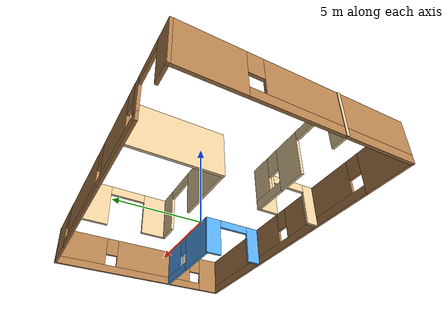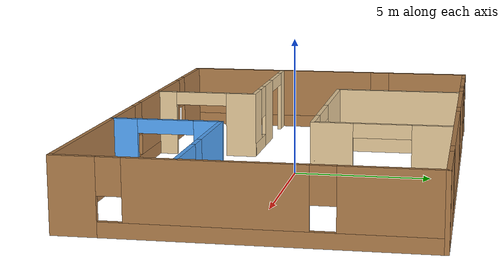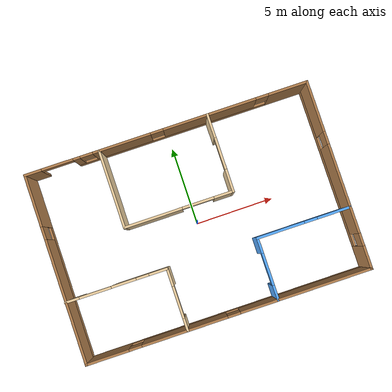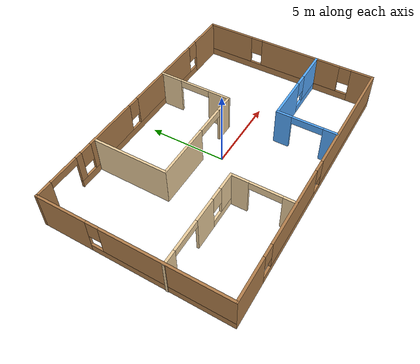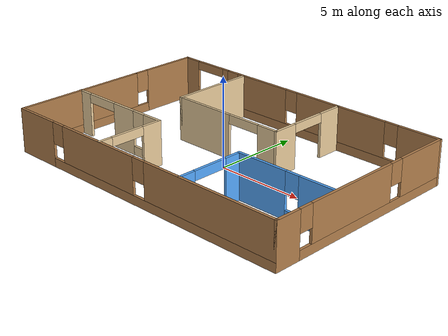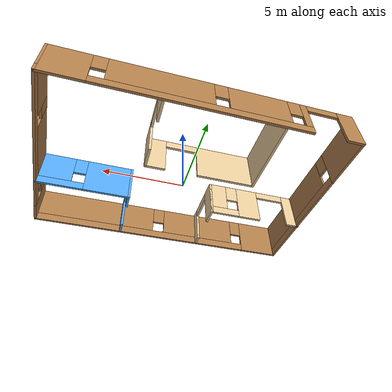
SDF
<?xml version='1.0'?>
<sdf version='1.6'>
  <model name='mybuilding'>
    <link name='Wall_25'>
      <pose frame=''>-8.90711 0 0 0 0 -1.5708</pose>
      <self_collide>0</self_collide>
      <kinematic>0</kinematic>
      <visual name='Wall_25_Visual_0'>
        <pose frame=''>-4.33953 0 1.25 0 -0 0</pose>
        <geometry>
          <box>
            <size>3.32095 0.15 2.5</size>
          </box>
        </geometry>
        <material>
          <script>
            <uri>file://media/materials/scripts/gazebo.material</uri>
            <name>Gazebo/Wood</name>
          </script>
          <ambient>1 1 1 1</ambient>
          <shader type='pixel'/>
          <diffuse>1 1 1 1</diffuse>
          <specular>0.2 0.2 0.2 1</specular>
          <emissive>0 0 0 1</emissive>
        </material>
        <meta>
          <layer>0</layer>
        </meta>
        <transparency>0</transparency>
        <cast_shadows>1</cast_shadows>
      </visual>
      <visual name='Wall_25_Visual_1'>
        <pose frame=''>1.66047 0 0.25 0 -0 0</pose>
        <geometry>
          <box>
            <size>8.67905 0.15 0.5</size>
          </box>
        </geometry>
        <material>
          <script>
            <uri>file://media/materials/scripts/gazebo.material</uri>
            <name>Gazebo/Wood</name>
          </script>
          <ambient>1 1 1 1</ambient>
          <shader type='pixel'/>
          <diffuse>1 1 1 1</diffuse>
          <specular>0.2 0.2 0.2 1</specular>
          <emissive>0 0 0 1</emissive>
        </material>
        <meta>
          <layer>0</layer>
        </meta>
        <transparency>0</transparency>
        <cast_shadows>1</cast_shadows>
      </visual>
      <visual name='Wall_25_Visual_2'>
        <pose frame=''>2.06047 0 1.5 0 -0 0</pose>
        <geometry>
          <box>
            <size>7.87905 0.15 2</size>
          </box>
        </geometry>
        <material>
          <script>
            <uri>file://media/materials/scripts/gazebo.material</uri>
            <name>Gazebo/Wood</name>
          </script>
          <ambient>1 1 1 1</ambient>
          <shader type='pixel'/>
          <diffuse>1 1 1 1</diffuse>
          <specular>0.2 0.2 0.2 1</specular>
          <emissive>0 0 0 1</emissive>
        </material>
        <meta>
          <layer>0</layer>
        </meta>
        <transparency>0</transparency>
        <cast_shadows>1</cast_shadows>
      </visual>
      <visual name='Wall_25_Visual_3'>
        <pose frame=''>-2.27905 0 1.9 0 -0 0</pose>
        <geometry>
          <box>
            <size>0.8 0.15 1.2</size>
          </box>
        </geometry>
        <material>
          <script>
            <uri>file://media/materials/scripts/gazebo.material</uri>
            <name>Gazebo/Wood</name>
          </script>
          <ambient>1 1 1 1</ambient>
          <shader type='pixel'/>
          <diffuse>1 1 1 1</diffuse>
          <specular>0.2 0.2 0.2 1</specular>
          <emissive>0 0 0 1</emissive>
        </material>
        <meta>
          <layer>0</layer>
        </meta>
        <transparency>0</transparency>
        <cast_shadows>1</cast_shadows>
      </visual>
      <collision name='Wall_25_Collision_0'>
        <laser_retro>0</laser_retro>
        <max_contacts>10</max_contacts>
        <pose frame=''>-4.33953 0 1.25 0 -0 0</pose>
        <geometry>
          <box>
            <size>3.32095 0.15 2.5</size>
          </box>
        </geometry>
        <surface>
          <friction>
            <ode>
              <mu>1</mu>
              <mu2>1</mu2>
              <fdir1>0 0 0</fdir1>
              <slip1>0</slip1>
              <slip2>0</slip2>
            </ode>
            <torsional>
              <coefficient>1</coefficient>
              <patch_radius>0</patch_radius>
              <surface_radius>0</surface_radius>
              <use_patch_radius>1</use_patch_radius>
              <ode>
                <slip>0</slip>
              </ode>
            </torsional>
          </friction>
          <bounce>
            <restitution_coefficient>0</restitution_coefficient>
            <threshold>1e+06</threshold>
          </bounce>
          <contact>
            <collide_without_contact>0</collide_without_contact>
            <collide_without_contact_bitmask>1</collide_without_contact_bitmask>
            <collide_bitmask>1</collide_bitmask>
            <ode>
              <soft_cfm>0</soft_cfm>
              <soft_erp>0.2</soft_erp>
              <kp>1e+13</kp>
              <kd>1</kd>
              <max_vel>0.01</max_vel>
              <min_depth>0</min_depth>
            </ode>
            <bullet>
              <split_impulse>1</split_impulse>
              <split_impulse_penetration_threshold>-0.01</split_impulse_penetration_threshold>
              <soft_cfm>0</soft_cfm>
              <soft_erp>0.2</soft_erp>
              <kp>1e+13</kp>
              <kd>1</kd>
            </bullet>
          </contact>
        </surface>
      </collision>
      <collision name='Wall_25_Collision_1'>
        <laser_retro>0</laser_retro>
        <max_contacts>10</max_contacts>
        <pose frame=''>1.66047 0 0.25 0 -0 0</pose>
        <geometry>
          <box>
            <size>8.67905 0.15 0.5</size>
          </box>
        </geometry>
        <surface>
          <friction>
            <ode>
              <mu>1</mu>
              <mu2>1</mu2>
              <fdir1>0 0 0</fdir1>
              <slip1>0</slip1>
              <slip2>0</slip2>
            </ode>
            <torsional>
              <coefficient>1</coefficient>
              <patch_radius>0</patch_radius>
              <surface_radius>0</surface_radius>
              <use_patch_radius>1</use_patch_radius>
              <ode>
                <slip>0</slip>
              </ode>
            </torsional>
          </friction>
          <bounce>
            <restitution_coefficient>0</restitution_coefficient>
            <threshold>1e+06</threshold>
          </bounce>
          <contact>
            <collide_without_contact>0</collide_without_contact>
            <collide_without_contact_bitmask>1</collide_without_contact_bitmask>
            <collide_bitmask>1</collide_bitmask>
            <ode>
              <soft_cfm>0</soft_cfm>
              <soft_erp>0.2</soft_erp>
              <kp>1e+13</kp>
              <kd>1</kd>
              <max_vel>0.01</max_vel>
              <min_depth>0</min_depth>
            </ode>
            <bullet>
              <split_impulse>1</split_impulse>
              <split_impulse_penetration_threshold>-0.01</split_impulse_penetration_threshold>
              <soft_cfm>0</soft_cfm>
              <soft_erp>0.2</soft_erp>
              <kp>1e+13</kp>
              <kd>1</kd>
            </bullet>
          </contact>
        </surface>
      </collision>
      <collision name='Wall_25_Collision_2'>
        <laser_retro>0</laser_retro>
        <max_contacts>10</max_contacts>
        <pose frame=''>2.06047 0 1.5 0 -0 0</pose>
        <geometry>
          <box>
            <size>7.87905 0.15 2</size>
          </box>
        </geometry>
        <surface>
          <friction>
            <ode>
              <mu>1</mu>
              <mu2>1</mu2>
              <fdir1>0 0 0</fdir1>
              <slip1>0</slip1>
              <slip2>0</slip2>
            </ode>
            <torsional>
              <coefficient>1</coefficient>
              <patch_radius>0</patch_radius>
              <surface_radius>0</surface_radius>
              <use_patch_radius>1</use_patch_radius>
              <ode>
                <slip>0</slip>
              </ode>
            </torsional>
          </friction>
          <bounce>
            <restitution_coefficient>0</restitution_coefficient>
            <threshold>1e+06</threshold>
          </bounce>
          <contact>
            <collide_without_contact>0</collide_without_contact>
            <collide_without_contact_bitmask>1</collide_without_contact_bitmask>
            <collide_bitmask>1</collide_bitmask>
            <ode>
              <soft_cfm>0</soft_cfm>
              <soft_erp>0.2</soft_erp>
              <kp>1e+13</kp>
              <kd>1</kd>
              <max_vel>0.01</max_vel>
              <min_depth>0</min_depth>
            </ode>
            <bullet>
              <split_impulse>1</split_impulse>
              <split_impulse_penetration_threshold>-0.01</split_impulse_penetration_threshold>
              <soft_cfm>0</soft_cfm>
              <soft_erp>0.2</soft_erp>
              <kp>1e+13</kp>
              <kd>1</kd>
            </bullet>
          </contact>
        </surface>
      </collision>
      <collision name='Wall_25_Collision_3'>
        <laser_retro>0</laser_retro>
        <max_contacts>10</max_contacts>
        <pose frame=''>-2.27905 0 1.9 0 -0 0</pose>
        <geometry>
          <box>
            <size>0.8 0.15 1.2</size>
          </box>
        </geometry>
        <surface>
          <friction>
            <ode>
              <mu>1</mu>
              <mu2>1</mu2>
              <fdir1>0 0 0</fdir1>
              <slip1>0</slip1>
              <slip2>0</slip2>
            </ode>
            <torsional>
              <coefficient>1</coefficient>
              <patch_radius>0</patch_radius>
              <surface_radius>0</surface_radius>
              <use_patch_radius>1</use_patch_radius>
              <ode>
                <slip>0</slip>
              </ode>
            </torsional>
          </friction>
          <bounce>
            <restitution_coefficient>0</restitution_coefficient>
            <threshold>1e+06</threshold>
          </bounce>
          <contact>
            <collide_without_contact>0</collide_without_contact>
            <collide_without_contact_bitmask>1</collide_without_contact_bitmask>
            <collide_bitmask>1</collide_bitmask>
            <ode>
              <soft_cfm>0</soft_cfm>
              <soft_erp>0.2</soft_erp>
              <kp>1e+13</kp>
              <kd>1</kd>
              <max_vel>0.01</max_vel>
              <min_depth>0</min_depth>
            </ode>
            <bullet>
              <split_impulse>1</split_impulse>
              <split_impulse_penetration_threshold>-0.01</split_impulse_penetration_threshold>
              <soft_cfm>0</soft_cfm>
              <soft_erp>0.2</soft_erp>
              <kp>1e+13</kp>
              <kd>1</kd>
            </bullet>
          </contact>
        </surface>
      </collision>
    </link>
    <link name='Wall_26'>
      <pose frame=''>0.01789 -5.925 0 0 -0 0</pose>
      <self_collide>0</self_collide>
      <kinematic>0</kinematic>
      <visual name='Wall_26_Visual_0'>
        <pose frame=''>-7.63172 0 1.25 0 -0 0</pose>
        <geometry>
          <box>
            <size>2.73657 0.15 2.5</size>
          </box>
        </geometry>
        <material>
          <script>
            <uri>file://media/materials/scripts/gazebo.material</uri>
            <name>Gazebo/Wood</name>
          </script>
          <ambient>1 1 1 1</ambient>
          <shader type='pixel'/>
          <diffuse>1 1 1 1</diffuse>
          <specular>0.2 0.2 0.2 1</specular>
          <emissive>0 0 0 1</emissive>
        </material>
        <meta>
          <layer>0</layer>
        </meta>
        <transparency>0</transparency>
        <cast_shadows>1</cast_shadows>
      </visual>
      <visual name='Wall_26_Visual_1'>
        <pose frame=''>1.36828 0 0.25 0 -0 0</pose>
        <geometry>
          <box>
            <size>15.2634 0.15 0.5</size>
          </box>
        </geometry>
        <material>
          <script>
            <uri>file://media/materials/scripts/gazebo.material</uri>
            <name>Gazebo/Wood</name>
          </script>
          <ambient>1 1 1 1</ambient>
          <shader type='pixel'/>
          <diffuse>1 1 1 1</diffuse>
          <specular>0.2 0.2 0.2 1</specular>
          <emissive>0 0 0 1</emissive>
        </material>
        <meta>
          <layer>0</layer>
        </meta>
        <transparency>0</transparency>
        <cast_shadows>1</cast_shadows>
      </visual>
      <visual name='Wall_26_Visual_2'>
        <pose frame=''>-2.78311 0 1.5 0 -0 0</pose>
        <geometry>
          <box>
            <size>5.36064 0.15 2</size>
          </box>
        </geometry>
        <material>
          <script>
            <uri>file://media/materials/scripts/gazebo.material</uri>
            <name>Gazebo/Wood</name>
          </script>
          <ambient>1 1 1 1</ambient>
          <shader type='pixel'/>
          <diffuse>1 1 1 1</diffuse>
          <specular>0.2 0.2 0.2 1</specular>
          <emissive>0 0 0 1</emissive>
        </material>
        <meta>
          <layer>0</layer>
        </meta>
        <transparency>0</transparency>
        <cast_shadows>1</cast_shadows>
      </visual>
      <visual name='Wall_26_Visual_3'>
        <pose frame=''>4.8486 0 1.5 0 -0 0</pose>
        <geometry>
          <box>
            <size>8.3028 0.15 2</size>
          </box>
        </geometry>
        <material>
          <script>
            <uri>file://media/materials/scripts/gazebo.material</uri>
            <name>Gazebo/Wood</name>
          </script>
          <ambient>1 1 1 1</ambient>
          <shader type='pixel'/>
          <diffuse>1 1 1 1</diffuse>
          <specular>0.2 0.2 0.2 1</specular>
          <emissive>0 0 0 1</emissive>
        </material>
        <meta>
          <layer>0</layer>
        </meta>
        <transparency>0</transparency>
        <cast_shadows>1</cast_shadows>
      </visual>
      <visual name='Wall_26_Visual_4'>
        <pose frame=''>-5.86343 0 1.9 0 -0 0</pose>
        <geometry>
          <box>
            <size>0.8 0.15 1.2</size>
          </box>
        </geometry>
        <material>
          <script>
            <uri>file://media/materials/scripts/gazebo.material</uri>
            <name>Gazebo/Wood</name>
          </script>
          <ambient>1 1 1 1</ambient>
          <shader type='pixel'/>
          <diffuse>1 1 1 1</diffuse>
          <specular>0.2 0.2 0.2 1</specular>
          <emissive>0 0 0 1</emissive>
        </material>
        <meta>
          <layer>0</layer>
        </meta>
        <transparency>0</transparency>
        <cast_shadows>1</cast_shadows>
      </visual>
      <visual name='Wall_26_Visual_5'>
        <pose frame=''>0.297204 0 1.9 0 -0 0</pose>
        <geometry>
          <box>
            <size>0.8 0.15 1.2</size>
          </box>
        </geometry>
        <material>
          <script>
            <uri>file://media/materials/scripts/gazebo.material</uri>
            <name>Gazebo/Wood</name>
          </script>
          <ambient>1 1 1 1</ambient>
          <shader type='pixel'/>
          <diffuse>1 1 1 1</diffuse>
          <specular>0.2 0.2 0.2 1</specular>
          <emissive>0 0 0 1</emissive>
        </material>
        <meta>
          <layer>0</layer>
        </meta>
        <transparency>0</transparency>
        <cast_shadows>1</cast_shadows>
      </visual>
      <collision name='Wall_26_Collision_0'>
        <laser_retro>0</laser_retro>
        <max_contacts>10</max_contacts>
        <pose frame=''>-7.63172 0 1.25 0 -0 0</pose>
        <geometry>
          <box>
            <size>2.73657 0.15 2.5</size>
          </box>
        </geometry>
        <surface>
          <friction>
            <ode>
              <mu>1</mu>
              <mu2>1</mu2>
              <fdir1>0 0 0</fdir1>
              <slip1>0</slip1>
              <slip2>0</slip2>
            </ode>
            <torsional>
              <coefficient>1</coefficient>
              <patch_radius>0</patch_radius>
              <surface_radius>0</surface_radius>
              <use_patch_radius>1</use_patch_radius>
              <ode>
                <slip>0</slip>
              </ode>
            </torsional>
          </friction>
          <bounce>
            <restitution_coefficient>0</restitution_coefficient>
            <threshold>1e+06</threshold>
          </bounce>
          <contact>
            <collide_without_contact>0</collide_without_contact>
            <collide_without_contact_bitmask>1</collide_without_contact_bitmask>
            <collide_bitmask>1</collide_bitmask>
            <ode>
              <soft_cfm>0</soft_cfm>
              <soft_erp>0.2</soft_erp>
              <kp>1e+13</kp>
              <kd>1</kd>
              <max_vel>0.01</max_vel>
              <min_depth>0</min_depth>
            </ode>
            <bullet>
              <split_impulse>1</split_impulse>
              <split_impulse_penetration_threshold>-0.01</split_impulse_penetration_threshold>
              <soft_cfm>0</soft_cfm>
              <soft_erp>0.2</soft_erp>
              <kp>1e+13</kp>
              <kd>1</kd>
            </bullet>
          </contact>
        </surface>
      </collision>
      <collision name='Wall_26_Collision_1'>
        <laser_retro>0</laser_retro>
        <max_contacts>10</max_contacts>
        <pose frame=''>1.36828 0 0.25 0 -0 0</pose>
        <geometry>
          <box>
            <size>15.2634 0.15 0.5</size>
          </box>
        </geometry>
        <surface>
          <friction>
            <ode>
              <mu>1</mu>
              <mu2>1</mu2>
              <fdir1>0 0 0</fdir1>
              <slip1>0</slip1>
              <slip2>0</slip2>
            </ode>
            <torsional>
              <coefficient>1</coefficient>
              <patch_radius>0</patch_radius>
              <surface_radius>0</surface_radius>
              <use_patch_radius>1</use_patch_radius>
              <ode>
                <slip>0</slip>
              </ode>
            </torsional>
          </friction>
          <bounce>
            <restitution_coefficient>0</restitution_coefficient>
            <threshold>1e+06</threshold>
          </bounce>
          <contact>
            <collide_without_contact>0</collide_without_contact>
            <collide_without_contact_bitmask>1</collide_without_contact_bitmask>
            <collide_bitmask>1</collide_bitmask>
            <ode>
              <soft_cfm>0</soft_cfm>
              <soft_erp>0.2</soft_erp>
              <kp>1e+13</kp>
              <kd>1</kd>
              <max_vel>0.01</max_vel>
              <min_depth>0</min_depth>
            </ode>
            <bullet>
              <split_impulse>1</split_impulse>
              <split_impulse_penetration_threshold>-0.01</split_impulse_penetration_threshold>
              <soft_cfm>0</soft_cfm>
              <soft_erp>0.2</soft_erp>
              <kp>1e+13</kp>
              <kd>1</kd>
            </bullet>
          </contact>
        </surface>
      </collision>
      <collision name='Wall_26_Collision_2'>
        <laser_retro>0</laser_retro>
        <max_contacts>10</max_contacts>
        <pose frame=''>-2.78311 0 1.5 0 -0 0</pose>
        <geometry>
          <box>
            <size>5.36064 0.15 2</size>
          </box>
        </geometry>
        <surface>
          <friction>
            <ode>
              <mu>1</mu>
              <mu2>1</mu2>
              <fdir1>0 0 0</fdir1>
              <slip1>0</slip1>
              <slip2>0</slip2>
            </ode>
            <torsional>
              <coefficient>1</coefficient>
              <patch_radius>0</patch_radius>
              <surface_radius>0</surface_radius>
              <use_patch_radius>1</use_patch_radius>
              <ode>
                <slip>0</slip>
              </ode>
            </torsional>
          </friction>
          <bounce>
            <restitution_coefficient>0</restitution_coefficient>
            <threshold>1e+06</threshold>
          </bounce>
          <contact>
            <collide_without_contact>0</collide_without_contact>
            <collide_without_contact_bitmask>1</collide_without_contact_bitmask>
            <collide_bitmask>1</collide_bitmask>
            <ode>
              <soft_cfm>0</soft_cfm>
              <soft_erp>0.2</soft_erp>
              <kp>1e+13</kp>
              <kd>1</kd>
              <max_vel>0.01</max_vel>
              <min_depth>0</min_depth>
            </ode>
            <bullet>
              <split_impulse>1</split_impulse>
              <split_impulse_penetration_threshold>-0.01</split_impulse_penetration_threshold>
              <soft_cfm>0</soft_cfm>
              <soft_erp>0.2</soft_erp>
              <kp>1e+13</kp>
              <kd>1</kd>
            </bullet>
          </contact>
        </surface>
      </collision>
      <collision name='Wall_26_Collision_3'>
        <laser_retro>0</laser_retro>
        <max_contacts>10</max_contacts>
        <pose frame=''>4.8486 0 1.5 0 -0 0</pose>
        <geometry>
          <box>
            <size>8.3028 0.15 2</size>
          </box>
        </geometry>
        <surface>
          <friction>
            <ode>
              <mu>1</mu>
              <mu2>1</mu2>
              <fdir1>0 0 0</fdir1>
              <slip1>0</slip1>
              <slip2>0</slip2>
            </ode>
            <torsional>
              <coefficient>1</coefficient>
              <patch_radius>0</patch_radius>
              <surface_radius>0</surface_radius>
              <use_patch_radius>1</use_patch_radius>
              <ode>
                <slip>0</slip>
              </ode>
            </torsional>
          </friction>
          <bounce>
            <restitution_coefficient>0</restitution_coefficient>
            <threshold>1e+06</threshold>
          </bounce>
          <contact>
            <collide_without_contact>0</collide_without_contact>
            <collide_without_contact_bitmask>1</collide_without_contact_bitmask>
            <collide_bitmask>1</collide_bitmask>
            <ode>
              <soft_cfm>0</soft_cfm>
              <soft_erp>0.2</soft_erp>
              <kp>1e+13</kp>
              <kd>1</kd>
              <max_vel>0.01</max_vel>
              <min_depth>0</min_depth>
            </ode>
            <bullet>
              <split_impulse>1</split_impulse>
              <split_impulse_penetration_threshold>-0.01</split_impulse_penetration_threshold>
              <soft_cfm>0</soft_cfm>
              <soft_erp>0.2</soft_erp>
              <kp>1e+13</kp>
              <kd>1</kd>
            </bullet>
          </contact>
        </surface>
      </collision>
      <collision name='Wall_26_Collision_4'>
        <laser_retro>0</laser_retro>
        <max_contacts>10</max_contacts>
        <pose frame=''>-5.86343 0 1.9 0 -0 0</pose>
        <geometry>
          <box>
            <size>0.8 0.15 1.2</size>
          </box>
        </geometry>
        <surface>
          <friction>
            <ode>
              <mu>1</mu>
              <mu2>1</mu2>
              <fdir1>0 0 0</fdir1>
              <slip1>0</slip1>
              <slip2>0</slip2>
            </ode>
            <torsional>
              <coefficient>1</coefficient>
              <patch_radius>0</patch_radius>
              <surface_radius>0</surface_radius>
              <use_patch_radius>1</use_patch_radius>
              <ode>
                <slip>0</slip>
              </ode>
            </torsional>
          </friction>
          <bounce>
            <restitution_coefficient>0</restitution_coefficient>
            <threshold>1e+06</threshold>
          </bounce>
          <contact>
            <collide_without_contact>0</collide_without_contact>
            <collide_without_contact_bitmask>1</collide_without_contact_bitmask>
            <collide_bitmask>1</collide_bitmask>
            <ode>
              <soft_cfm>0</soft_cfm>
              <soft_erp>0.2</soft_erp>
              <kp>1e+13</kp>
              <kd>1</kd>
              <max_vel>0.01</max_vel>
              <min_depth>0</min_depth>
            </ode>
            <bullet>
              <split_impulse>1</split_impulse>
              <split_impulse_penetration_threshold>-0.01</split_impulse_penetration_threshold>
              <soft_cfm>0</soft_cfm>
              <soft_erp>0.2</soft_erp>
              <kp>1e+13</kp>
              <kd>1</kd>
            </bullet>
          </contact>
        </surface>
      </collision>
      <collision name='Wall_26_Collision_5'>
        <laser_retro>0</laser_retro>
        <max_contacts>10</max_contacts>
        <pose frame=''>0.297204 0 1.9 0 -0 0</pose>
        <geometry>
          <box>
            <size>0.8 0.15 1.2</size>
          </box>
        </geometry>
        <surface>
          <friction>
            <ode>
              <mu>1</mu>
              <mu2>1</mu2>
              <fdir1>0 0 0</fdir1>
              <slip1>0</slip1>
              <slip2>0</slip2>
            </ode>
            <torsional>
              <coefficient>1</coefficient>
              <patch_radius>0</patch_radius>
              <surface_radius>0</surface_radius>
              <use_patch_radius>1</use_patch_radius>
              <ode>
                <slip>0</slip>
              </ode>
            </torsional>
          </friction>
          <bounce>
            <restitution_coefficient>0</restitution_coefficient>
            <threshold>1e+06</threshold>
          </bounce>
          <contact>
            <collide_without_contact>0</collide_without_contact>
            <collide_without_contact_bitmask>1</collide_without_contact_bitmask>
            <collide_bitmask>1</collide_bitmask>
            <ode>
              <soft_cfm>0</soft_cfm>
              <soft_erp>0.2</soft_erp>
              <kp>1e+13</kp>
              <kd>1</kd>
              <max_vel>0.01</max_vel>
              <min_depth>0</min_depth>
            </ode>
            <bullet>
              <split_impulse>1</split_impulse>
              <split_impulse_penetration_threshold>-0.01</split_impulse_penetration_threshold>
              <soft_cfm>0</soft_cfm>
              <soft_erp>0.2</soft_erp>
              <kp>1e+13</kp>
              <kd>1</kd>
            </bullet>
          </contact>
        </surface>
      </collision>
    </link>
    <link name='Wall_27'>
      <pose frame=''>8.94289 0 0 0 -0 1.5708</pose>
      <self_collide>0</self_collide>
      <kinematic>0</kinematic>
      <visual name='Wall_27_Visual_0'>
        <pose frame=''>-5.24969 0 1.25 0 -0 0</pose>
        <geometry>
          <box>
            <size>1.50062 0.15 2.5</size>
          </box>
        </geometry>
        <material>
          <script>
            <uri>file://media/materials/scripts/gazebo.material</uri>
            <name>Gazebo/Wood</name>
          </script>
          <ambient>1 1 1 1</ambient>
          <shader type='pixel'/>
          <diffuse>1 1 1 1</diffuse>
          <specular>0.2 0.2 0.2 1</specular>
          <emissive>0 0 0 1</emissive>
        </material>
        <meta>
          <layer>0</layer>
        </meta>
        <transparency>0</transparency>
        <cast_shadows>1</cast_shadows>
      </visual>
      <visual name='Wall_27_Visual_1'>
        <pose frame=''>0.750309 0 0.25 0 -0 0</pose>
        <geometry>
          <box>
            <size>10.4994 0.15 0.5</size>
          </box>
        </geometry>
        <material>
          <script>
            <uri>file://media/materials/scripts/gazebo.material</uri>
            <name>Gazebo/Wood</name>
          </script>
          <ambient>1 1 1 1</ambient>
          <shader type='pixel'/>
          <diffuse>1 1 1 1</diffuse>
          <specular>0.2 0.2 0.2 1</specular>
          <emissive>0 0 0 1</emissive>
        </material>
        <meta>
          <layer>0</layer>
        </meta>
        <transparency>0</transparency>
        <cast_shadows>1</cast_shadows>
      </visual>
      <visual name='Wall_27_Visual_2'>
        <pose frame=''>-0.87905 0 1.5 0 -0 0</pose>
        <geometry>
          <box>
            <size>5.64067 0.15 2</size>
          </box>
        </geometry>
        <material>
          <script>
            <uri>file://media/materials/scripts/gazebo.material</uri>
            <name>Gazebo/Wood</name>
          </script>
          <ambient>1 1 1 1</ambient>
          <shader type='pixel'/>
          <diffuse>1 1 1 1</diffuse>
          <specular>0.2 0.2 0.2 1</specular>
          <emissive>0 0 0 1</emissive>
        </material>
        <meta>
          <layer>0</layer>
        </meta>
        <transparency>0</transparency>
        <cast_shadows>1</cast_shadows>
      </visual>
      <visual name='Wall_27_Visual_3'>
        <pose frame=''>4.37064 0 1.5 0 -0 0</pose>
        <geometry>
          <box>
            <size>3.25872 0.15 2</size>
          </box>
        </geometry>
        <material>
          <script>
            <uri>file://media/materials/scripts/gazebo.material</uri>
            <name>Gazebo/Wood</name>
          </script>
          <ambient>1 1 1 1</ambient>
          <shader type='pixel'/>
          <diffuse>1 1 1 1</diffuse>
          <specular>0.2 0.2 0.2 1</specular>
          <emissive>0 0 0 1</emissive>
        </material>
        <meta>
          <layer>0</layer>
        </meta>
        <transparency>0</transparency>
        <cast_shadows>1</cast_shadows>
      </visual>
      <visual name='Wall_27_Visual_4'>
        <pose frame=''>-4.09938 0 1.9 0 -0 0</pose>
        <geometry>
          <box>
            <size>0.8 0.15 1.2</size>
          </box>
        </geometry>
        <material>
          <script>
            <uri>file://media/materials/scripts/gazebo.material</uri>
            <name>Gazebo/Wood</name>
          </script>
          <ambient>1 1 1 1</ambient>
          <shader type='pixel'/>
          <diffuse>1 1 1 1</diffuse>
          <specular>0.2 0.2 0.2 1</specular>
          <emissive>0 0 0 1</emissive>
        </material>
        <meta>
          <layer>0</layer>
        </meta>
        <transparency>0</transparency>
        <cast_shadows>1</cast_shadows>
      </visual>
      <visual name='Wall_27_Visual_5'>
        <pose frame=''>2.34128 0 1.9 0 -0 0</pose>
        <geometry>
          <box>
            <size>0.8 0.15 1.2</size>
          </box>
        </geometry>
        <material>
          <script>
            <uri>file://media/materials/scripts/gazebo.material</uri>
            <name>Gazebo/Wood</name>
          </script>
          <ambient>1 1 1 1</ambient>
          <shader type='pixel'/>
          <diffuse>1 1 1 1</diffuse>
          <specular>0.2 0.2 0.2 1</specular>
          <emissive>0 0 0 1</emissive>
        </material>
        <meta>
          <layer>0</layer>
        </meta>
        <transparency>0</transparency>
        <cast_shadows>1</cast_shadows>
      </visual>
      <collision name='Wall_27_Collision_0'>
        <laser_retro>0</laser_retro>
        <max_contacts>10</max_contacts>
        <pose frame=''>-5.24969 0 1.25 0 -0 0</pose>
        <geometry>
          <box>
            <size>1.50062 0.15 2.5</size>
          </box>
        </geometry>
        <surface>
          <friction>
            <ode>
              <mu>1</mu>
              <mu2>1</mu2>
              <fdir1>0 0 0</fdir1>
              <slip1>0</slip1>
              <slip2>0</slip2>
            </ode>
            <torsional>
              <coefficient>1</coefficient>
              <patch_radius>0</patch_radius>
              <surface_radius>0</surface_radius>
              <use_patch_radius>1</use_patch_radius>
              <ode>
                <slip>0</slip>
              </ode>
            </torsional>
          </friction>
          <bounce>
            <restitution_coefficient>0</restitution_coefficient>
            <threshold>1e+06</threshold>
          </bounce>
          <contact>
            <collide_without_contact>0</collide_without_contact>
            <collide_without_contact_bitmask>1</collide_without_contact_bitmask>
            <collide_bitmask>1</collide_bitmask>
            <ode>
              <soft_cfm>0</soft_cfm>
              <soft_erp>0.2</soft_erp>
              <kp>1e+13</kp>
              <kd>1</kd>
              <max_vel>0.01</max_vel>
              <min_depth>0</min_depth>
            </ode>
            <bullet>
              <split_impulse>1</split_impulse>
              <split_impulse_penetration_threshold>-0.01</split_impulse_penetration_threshold>
              <soft_cfm>0</soft_cfm>
              <soft_erp>0.2</soft_erp>
              <kp>1e+13</kp>
              <kd>1</kd>
            </bullet>
          </contact>
        </surface>
      </collision>
      <collision name='Wall_27_Collision_1'>
        <laser_retro>0</laser_retro>
        <max_contacts>10</max_contacts>
        <pose frame=''>0.750309 0 0.25 0 -0 0</pose>
        <geometry>
          <box>
            <size>10.4994 0.15 0.5</size>
          </box>
        </geometry>
        <surface>
          <friction>
            <ode>
              <mu>1</mu>
              <mu2>1</mu2>
              <fdir1>0 0 0</fdir1>
              <slip1>0</slip1>
              <slip2>0</slip2>
            </ode>
            <torsional>
              <coefficient>1</coefficient>
              <patch_radius>0</patch_radius>
              <surface_radius>0</surface_radius>
              <use_patch_radius>1</use_patch_radius>
              <ode>
                <slip>0</slip>
              </ode>
            </torsional>
          </friction>
          <bounce>
            <restitution_coefficient>0</restitution_coefficient>
            <threshold>1e+06</threshold>
          </bounce>
          <contact>
            <collide_without_contact>0</collide_without_contact>
            <collide_without_contact_bitmask>1</collide_without_contact_bitmask>
            <collide_bitmask>1</collide_bitmask>
            <ode>
              <soft_cfm>0</soft_cfm>
              <soft_erp>0.2</soft_erp>
              <kp>1e+13</kp>
              <kd>1</kd>
              <max_vel>0.01</max_vel>
              <min_depth>0</min_depth>
            </ode>
            <bullet>
              <split_impulse>1</split_impulse>
              <split_impulse_penetration_threshold>-0.01</split_impulse_penetration_threshold>
              <soft_cfm>0</soft_cfm>
              <soft_erp>0.2</soft_erp>
              <kp>1e+13</kp>
              <kd>1</kd>
            </bullet>
          </contact>
        </surface>
      </collision>
      <collision name='Wall_27_Collision_2'>
        <laser_retro>0</laser_retro>
        <max_contacts>10</max_contacts>
        <pose frame=''>-0.87905 0 1.5 0 -0 0</pose>
        <geometry>
          <box>
            <size>5.64067 0.15 2</size>
          </box>
        </geometry>
        <surface>
          <friction>
            <ode>
              <mu>1</mu>
              <mu2>1</mu2>
              <fdir1>0 0 0</fdir1>
              <slip1>0</slip1>
              <slip2>0</slip2>
            </ode>
            <torsional>
              <coefficient>1</coefficient>
              <patch_radius>0</patch_radius>
              <surface_radius>0</surface_radius>
              <use_patch_radius>1</use_patch_radius>
              <ode>
                <slip>0</slip>
              </ode>
            </torsional>
          </friction>
          <bounce>
            <restitution_coefficient>0</restitution_coefficient>
            <threshold>1e+06</threshold>
          </bounce>
          <contact>
            <collide_without_contact>0</collide_without_contact>
            <collide_without_contact_bitmask>1</collide_without_contact_bitmask>
            <collide_bitmask>1</collide_bitmask>
            <ode>
              <soft_cfm>0</soft_cfm>
              <soft_erp>0.2</soft_erp>
              <kp>1e+13</kp>
              <kd>1</kd>
              <max_vel>0.01</max_vel>
              <min_depth>0</min_depth>
            </ode>
            <bullet>
              <split_impulse>1</split_impulse>
              <split_impulse_penetration_threshold>-0.01</split_impulse_penetration_threshold>
              <soft_cfm>0</soft_cfm>
              <soft_erp>0.2</soft_erp>
              <kp>1e+13</kp>
              <kd>1</kd>
            </bullet>
          </contact>
        </surface>
      </collision>
      <collision name='Wall_27_Collision_3'>
        <laser_retro>0</laser_retro>
        <max_contacts>10</max_contacts>
        <pose frame=''>4.37064 0 1.5 0 -0 0</pose>
        <geometry>
          <box>
            <size>3.25872 0.15 2</size>
          </box>
        </geometry>
        <surface>
          <friction>
            <ode>
              <mu>1</mu>
              <mu2>1</mu2>
              <fdir1>0 0 0</fdir1>
              <slip1>0</slip1>
              <slip2>0</slip2>
            </ode>
            <torsional>
              <coefficient>1</coefficient>
              <patch_radius>0</patch_radius>
              <surface_radius>0</surface_radius>
              <use_patch_radius>1</use_patch_radius>
              <ode>
                <slip>0</slip>
              </ode>
            </torsional>
          </friction>
          <bounce>
            <restitution_coefficient>0</restitution_coefficient>
            <threshold>1e+06</threshold>
          </bounce>
          <contact>
            <collide_without_contact>0</collide_without_contact>
            <collide_without_contact_bitmask>1</collide_without_contact_bitmask>
            <collide_bitmask>1</collide_bitmask>
            <ode>
              <soft_cfm>0</soft_cfm>
              <soft_erp>0.2</soft_erp>
              <kp>1e+13</kp>
              <kd>1</kd>
              <max_vel>0.01</max_vel>
              <min_depth>0</min_depth>
            </ode>
            <bullet>
              <split_impulse>1</split_impulse>
              <split_impulse_penetration_threshold>-0.01</split_impulse_penetration_threshold>
              <soft_cfm>0</soft_cfm>
              <soft_erp>0.2</soft_erp>
              <kp>1e+13</kp>
              <kd>1</kd>
            </bullet>
          </contact>
        </surface>
      </collision>
      <collision name='Wall_27_Collision_4'>
        <laser_retro>0</laser_retro>
        <max_contacts>10</max_contacts>
        <pose frame=''>-4.09938 0 1.9 0 -0 0</pose>
        <geometry>
          <box>
            <size>0.8 0.15 1.2</size>
          </box>
        </geometry>
        <surface>
          <friction>
            <ode>
              <mu>1</mu>
              <mu2>1</mu2>
              <fdir1>0 0 0</fdir1>
              <slip1>0</slip1>
              <slip2>0</slip2>
            </ode>
            <torsional>
              <coefficient>1</coefficient>
              <patch_radius>0</patch_radius>
              <surface_radius>0</surface_radius>
              <use_patch_radius>1</use_patch_radius>
              <ode>
                <slip>0</slip>
              </ode>
            </torsional>
          </friction>
          <bounce>
            <restitution_coefficient>0</restitution_coefficient>
            <threshold>1e+06</threshold>
          </bounce>
          <contact>
            <collide_without_contact>0</collide_without_contact>
            <collide_without_contact_bitmask>1</collide_without_contact_bitmask>
            <collide_bitmask>1</collide_bitmask>
            <ode>
              <soft_cfm>0</soft_cfm>
              <soft_erp>0.2</soft_erp>
              <kp>1e+13</kp>
              <kd>1</kd>
              <max_vel>0.01</max_vel>
              <min_depth>0</min_depth>
            </ode>
            <bullet>
              <split_impulse>1</split_impulse>
              <split_impulse_penetration_threshold>-0.01</split_impulse_penetration_threshold>
              <soft_cfm>0</soft_cfm>
              <soft_erp>0.2</soft_erp>
              <kp>1e+13</kp>
              <kd>1</kd>
            </bullet>
          </contact>
        </surface>
      </collision>
      <collision name='Wall_27_Collision_5'>
        <laser_retro>0</laser_retro>
        <max_contacts>10</max_contacts>
        <pose frame=''>2.34128 0 1.9 0 -0 0</pose>
        <geometry>
          <box>
            <size>0.8 0.15 1.2</size>
          </box>
        </geometry>
        <surface>
          <friction>
            <ode>
              <mu>1</mu>
              <mu2>1</mu2>
              <fdir1>0 0 0</fdir1>
              <slip1>0</slip1>
              <slip2>0</slip2>
            </ode>
            <torsional>
              <coefficient>1</coefficient>
              <patch_radius>0</patch_radius>
              <surface_radius>0</surface_radius>
              <use_patch_radius>1</use_patch_radius>
              <ode>
                <slip>0</slip>
              </ode>
            </torsional>
          </friction>
          <bounce>
            <restitution_coefficient>0</restitution_coefficient>
            <threshold>1e+06</threshold>
          </bounce>
          <contact>
            <collide_without_contact>0</collide_without_contact>
            <collide_without_contact_bitmask>1</collide_without_contact_bitmask>
            <collide_bitmask>1</collide_bitmask>
            <ode>
              <soft_cfm>0</soft_cfm>
              <soft_erp>0.2</soft_erp>
              <kp>1e+13</kp>
              <kd>1</kd>
              <max_vel>0.01</max_vel>
              <min_depth>0</min_depth>
            </ode>
            <bullet>
              <split_impulse>1</split_impulse>
              <split_impulse_penetration_threshold>-0.01</split_impulse_penetration_threshold>
              <soft_cfm>0</soft_cfm>
              <soft_erp>0.2</soft_erp>
              <kp>1e+13</kp>
              <kd>1</kd>
            </bullet>
          </contact>
        </surface>
      </collision>
    </link>
    <link name='Wall_28'>
      <pose frame=''>0.01789 5.925 0 0 -0 3.14159</pose>
      <self_collide>0</self_collide>
      <kinematic>0</kinematic>
      <visual name='Wall_28_Visual_0'>
        <pose frame=''>-7.74223 0 1.25 0 -0 0</pose>
        <geometry>
          <box>
            <size>2.51553 0.15 2.5</size>
          </box>
        </geometry>
        <material>
          <script>
            <uri>file://media/materials/scripts/gazebo.material</uri>
            <name>Gazebo/Wood</name>
          </script>
          <ambient>1 1 1 1</ambient>
          <shader type='pixel'/>
          <diffuse>1 1 1 1</diffuse>
          <specular>0.2 0.2 0.2 1</specular>
          <emissive>0 0 0 1</emissive>
        </material>
        <meta>
          <layer>0</layer>
        </meta>
        <transparency>0</transparency>
        <cast_shadows>1</cast_shadows>
      </visual>
      <visual name='Wall_28_Visual_1'>
        <pose frame=''>8.4451 0 1.25 0 -0 0</pose>
        <geometry>
          <box>
            <size>1.1098 0.15 2.5</size>
          </box>
        </geometry>
        <material>
          <script>
            <uri>file://media/materials/scripts/gazebo.material</uri>
            <name>Gazebo/Wood</name>
          </script>
          <ambient>1 1 1 1</ambient>
          <shader type='pixel'/>
          <diffuse>1 1 1 1</diffuse>
          <specular>0.2 0.2 0.2 1</specular>
          <emissive>0 0 0 1</emissive>
        </material>
        <meta>
          <layer>0</layer>
        </meta>
        <transparency>0</transparency>
        <cast_shadows>1</cast_shadows>
      </visual>
      <visual name='Wall_28_Visual_2'>
        <pose frame=''>-0.297132 0 0.25 0 -0 0</pose>
        <geometry>
          <box>
            <size>12.3747 0.15 0.5</size>
          </box>
        </geometry>
        <material>
          <script>
            <uri>file://media/materials/scripts/gazebo.material</uri>
            <name>Gazebo/Wood</name>
          </script>
          <ambient>1 1 1 1</ambient>
          <shader type='pixel'/>
          <diffuse>1 1 1 1</diffuse>
          <specular>0.2 0.2 0.2 1</specular>
          <emissive>0 0 0 1</emissive>
        </material>
        <meta>
          <layer>0</layer>
        </meta>
        <transparency>0</transparency>
        <cast_shadows>1</cast_shadows>
      </visual>
      <visual name='Wall_28_Visual_3'>
        <pose frame=''>-2.73968 0 1.5 0 -0 0</pose>
        <geometry>
          <box>
            <size>5.88958 0.15 2</size>
          </box>
        </geometry>
        <material>
          <script>
            <uri>file://media/materials/scripts/gazebo.material</uri>
            <name>Gazebo/Wood</name>
          </script>
          <ambient>1 1 1 1</ambient>
          <shader type='pixel'/>
          <diffuse>1 1 1 1</diffuse>
          <specular>0.2 0.2 0.2 1</specular>
          <emissive>0 0 0 1</emissive>
        </material>
        <meta>
          <layer>0</layer>
        </meta>
        <transparency>0</transparency>
        <cast_shadows>1</cast_shadows>
      </visual>
      <visual name='Wall_28_Visual_4'>
        <pose frame=''>2.82979 0 1.5 0 -0 0</pose>
        <geometry>
          <box>
            <size>3.64935 0.15 2</size>
          </box>
        </geometry>
        <material>
          <script>
            <uri>file://media/materials/scripts/gazebo.material</uri>
            <name>Gazebo/Wood</name>
          </script>
          <ambient>1 1 1 1</ambient>
          <shader type='pixel'/>
          <diffuse>1 1 1 1</diffuse>
          <specular>0.2 0.2 0.2 1</specular>
          <emissive>0 0 0 1</emissive>
        </material>
        <meta>
          <layer>0</layer>
        </meta>
        <transparency>0</transparency>
        <cast_shadows>1</cast_shadows>
      </visual>
      <visual name='Wall_28_Visual_5'>
        <pose frame=''>5.67233 0 1.5 0 -0 0</pose>
        <geometry>
          <box>
            <size>0.435745 0.15 2</size>
          </box>
        </geometry>
        <material>
          <script>
            <uri>file://media/materials/scripts/gazebo.material</uri>
            <name>Gazebo/Wood</name>
          </script>
          <ambient>1 1 1 1</ambient>
          <shader type='pixel'/>
          <diffuse>1 1 1 1</diffuse>
          <specular>0.2 0.2 0.2 1</specular>
          <emissive>0 0 0 1</emissive>
        </material>
        <meta>
          <layer>0</layer>
        </meta>
        <transparency>0</transparency>
        <cast_shadows>1</cast_shadows>
      </visual>
      <visual name='Wall_28_Visual_6'>
        <pose frame=''>-6.08447 0 1.9 0 -0 0</pose>
        <geometry>
          <box>
            <size>0.8 0.15 1.2</size>
          </box>
        </geometry>
        <material>
          <script>
            <uri>file://media/materials/scripts/gazebo.material</uri>
            <name>Gazebo/Wood</name>
          </script>
          <ambient>1 1 1 1</ambient>
          <shader type='pixel'/>
          <diffuse>1 1 1 1</diffuse>
          <specular>0.2 0.2 0.2 1</specular>
          <emissive>0 0 0 1</emissive>
        </material>
        <meta>
          <layer>0</layer>
        </meta>
        <transparency>0</transparency>
        <cast_shadows>1</cast_shadows>
      </visual>
      <visual name='Wall_28_Visual_7'>
        <pose frame=''>0.605112 0 1.9 0 -0 0</pose>
        <geometry>
          <box>
            <size>0.8 0.15 1.2</size>
          </box>
        </geometry>
        <material>
          <script>
            <uri>file://media/materials/scripts/gazebo.material</uri>
            <name>Gazebo/Wood</name>
          </script>
          <ambient>1 1 1 1</ambient>
          <shader type='pixel'/>
          <diffuse>1 1 1 1</diffuse>
          <specular>0.2 0.2 0.2 1</specular>
          <emissive>0 0 0 1</emissive>
        </material>
        <meta>
          <layer>0</layer>
        </meta>
        <transparency>0</transparency>
        <cast_shadows>1</cast_shadows>
      </visual>
      <visual name='Wall_28_Visual_8'>
        <pose frame=''>5.05446 0 1.9 0 -0 0</pose>
        <geometry>
          <box>
            <size>0.8 0.15 1.2</size>
          </box>
        </geometry>
        <material>
          <script>
            <uri>file://media/materials/scripts/gazebo.material</uri>
            <name>Gazebo/Wood</name>
          </script>
          <ambient>1 1 1 1</ambient>
          <shader type='pixel'/>
          <diffuse>1 1 1 1</diffuse>
          <specular>0.2 0.2 0.2 1</specular>
          <emissive>0 0 0 1</emissive>
        </material>
        <meta>
          <layer>0</layer>
        </meta>
        <transparency>0</transparency>
        <cast_shadows>1</cast_shadows>
      </visual>
      <visual name='Wall_28_Visual_9'>
        <pose frame=''>6.8902 0 2.25 0 -0 0</pose>
        <geometry>
          <box>
            <size>2 0.15 0.5</size>
          </box>
        </geometry>
        <material>
          <script>
            <uri>file://media/materials/scripts/gazebo.material</uri>
            <name>Gazebo/Wood</name>
          </script>
          <ambient>1 1 1 1</ambient>
          <shader type='pixel'/>
          <diffuse>1 1 1 1</diffuse>
          <specular>0.2 0.2 0.2 1</specular>
          <emissive>0 0 0 1</emissive>
        </material>
        <meta>
          <layer>0</layer>
        </meta>
        <transparency>0</transparency>
        <cast_shadows>1</cast_shadows>
      </visual>
      <collision name='Wall_28_Collision_0'>
        <laser_retro>0</laser_retro>
        <max_contacts>10</max_contacts>
        <pose frame=''>-7.74223 0 1.25 0 -0 0</pose>
        <geometry>
          <box>
            <size>2.51553 0.15 2.5</size>
          </box>
        </geometry>
        <surface>
          <friction>
            <ode>
              <mu>1</mu>
              <mu2>1</mu2>
              <fdir1>0 0 0</fdir1>
              <slip1>0</slip1>
              <slip2>0</slip2>
            </ode>
            <torsional>
              <coefficient>1</coefficient>
              <patch_radius>0</patch_radius>
              <surface_radius>0</surface_radius>
              <use_patch_radius>1</use_patch_radius>
              <ode>
                <slip>0</slip>
              </ode>
            </torsional>
          </friction>
          <bounce>
            <restitution_coefficient>0</restitution_coefficient>
            <threshold>1e+06</threshold>
          </bounce>
          <contact>
            <collide_without_contact>0</collide_without_contact>
            <collide_without_contact_bitmask>1</collide_without_contact_bitmask>
            <collide_bitmask>1</collide_bitmask>
            <ode>
              <soft_cfm>0</soft_cfm>
              <soft_erp>0.2</soft_erp>
              <kp>1e+13</kp>
              <kd>1</kd>
              <max_vel>0.01</max_vel>
              <min_depth>0</min_depth>
            </ode>
            <bullet>
              <split_impulse>1</split_impulse>
              <split_impulse_penetration_threshold>-0.01</split_impulse_penetration_threshold>
              <soft_cfm>0</soft_cfm>
              <soft_erp>0.2</soft_erp>
              <kp>1e+13</kp>
              <kd>1</kd>
            </bullet>
          </contact>
        </surface>
      </collision>
      <collision name='Wall_28_Collision_1'>
        <laser_retro>0</laser_retro>
        <max_contacts>10</max_contacts>
        <pose frame=''>8.4451 0 1.25 0 -0 0</pose>
        <geometry>
          <box>
            <size>1.1098 0.15 2.5</size>
          </box>
        </geometry>
        <surface>
          <friction>
            <ode>
              <mu>1</mu>
              <mu2>1</mu2>
              <fdir1>0 0 0</fdir1>
              <slip1>0</slip1>
              <slip2>0</slip2>
            </ode>
            <torsional>
              <coefficient>1</coefficient>
              <patch_radius>0</patch_radius>
              <surface_radius>0</surface_radius>
              <use_patch_radius>1</use_patch_radius>
              <ode>
                <slip>0</slip>
              </ode>
            </torsional>
          </friction>
          <bounce>
            <restitution_coefficient>0</restitution_coefficient>
            <threshold>1e+06</threshold>
          </bounce>
          <contact>
            <collide_without_contact>0</collide_without_contact>
            <collide_without_contact_bitmask>1</collide_without_contact_bitmask>
            <collide_bitmask>1</collide_bitmask>
            <ode>
              <soft_cfm>0</soft_cfm>
              <soft_erp>0.2</soft_erp>
              <kp>1e+13</kp>
              <kd>1</kd>
              <max_vel>0.01</max_vel>
              <min_depth>0</min_depth>
            </ode>
            <bullet>
              <split_impulse>1</split_impulse>
              <split_impulse_penetration_threshold>-0.01</split_impulse_penetration_threshold>
              <soft_cfm>0</soft_cfm>
              <soft_erp>0.2</soft_erp>
              <kp>1e+13</kp>
              <kd>1</kd>
            </bullet>
          </contact>
        </surface>
      </collision>
      <collision name='Wall_28_Collision_2'>
        <laser_retro>0</laser_retro>
        <max_contacts>10</max_contacts>
        <pose frame=''>-0.297132 0 0.25 0 -0 0</pose>
        <geometry>
          <box>
            <size>12.3747 0.15 0.5</size>
          </box>
        </geometry>
        <surface>
          <friction>
            <ode>
              <mu>1</mu>
              <mu2>1</mu2>
              <fdir1>0 0 0</fdir1>
              <slip1>0</slip1>
              <slip2>0</slip2>
            </ode>
            <torsional>
              <coefficient>1</coefficient>
              <patch_radius>0</patch_radius>
              <surface_radius>0</surface_radius>
              <use_patch_radius>1</use_patch_radius>
              <ode>
                <slip>0</slip>
              </ode>
            </torsional>
          </friction>
          <bounce>
            <restitution_coefficient>0</restitution_coefficient>
            <threshold>1e+06</threshold>
          </bounce>
          <contact>
            <collide_without_contact>0</collide_without_contact>
            <collide_without_contact_bitmask>1</collide_without_contact_bitmask>
            <collide_bitmask>1</collide_bitmask>
            <ode>
              <soft_cfm>0</soft_cfm>
              <soft_erp>0.2</soft_erp>
              <kp>1e+13</kp>
              <kd>1</kd>
              <max_vel>0.01</max_vel>
              <min_depth>0</min_depth>
            </ode>
            <bullet>
              <split_impulse>1</split_impulse>
              <split_impulse_penetration_threshold>-0.01</split_impulse_penetration_threshold>
              <soft_cfm>0</soft_cfm>
              <soft_erp>0.2</soft_erp>
              <kp>1e+13</kp>
              <kd>1</kd>
            </bullet>
          </contact>
        </surface>
      </collision>
      <collision name='Wall_28_Collision_4'>
        <laser_retro>0</laser_retro>
        <max_contacts>10</max_contacts>
        <pose frame=''>2.82979 0 1.5 0 -0 0</pose>
        <geometry>
          <box>
            <size>3.64935 0.15 2</size>
          </box>
        </geometry>
        <surface>
          <friction>
            <ode>
              <mu>1</mu>
              <mu2>1</mu2>
              <fdir1>0 0 0</fdir1>
              <slip1>0</slip1>
              <slip2>0</slip2>
            </ode>
            <torsional>
              <coefficient>1</coefficient>
              <patch_radius>0</patch_radius>
              <surface_radius>0</surface_radius>
              <use_patch_radius>1</use_patch_radius>
              <ode>
                <slip>0</slip>
              </ode>
            </torsional>
          </friction>
          <bounce>
            <restitution_coefficient>0</restitution_coefficient>
            <threshold>1e+06</threshold>
          </bounce>
          <contact>
            <collide_without_contact>0</collide_without_contact>
            <collide_without_contact_bitmask>1</collide_without_contact_bitmask>
            <collide_bitmask>1</collide_bitmask>
            <ode>
              <soft_cfm>0</soft_cfm>
              <soft_erp>0.2</soft_erp>
              <kp>1e+13</kp>
              <kd>1</kd>
              <max_vel>0.01</max_vel>
              <min_depth>0</min_depth>
            </ode>
            <bullet>
              <split_impulse>1</split_impulse>
              <split_impulse_penetration_threshold>-0.01</split_impulse_penetration_threshold>
              <soft_cfm>0</soft_cfm>
              <soft_erp>0.2</soft_erp>
              <kp>1e+13</kp>
              <kd>1</kd>
            </bullet>
          </contact>
        </surface>
      </collision>
      <collision name='Wall_28_Collision_3'>
        <laser_retro>0</laser_retro>
        <max_contacts>10</max_contacts>
        <pose frame=''>-2.73968 0 1.5 0 -0 0</pose>
        <geometry>
          <box>
            <size>5.88958 0.15 2</size>
          </box>
        </geometry>
        <surface>
          <friction>
            <ode>
              <mu>1</mu>
              <mu2>1</mu2>
              <fdir1>0 0 0</fdir1>
              <slip1>0</slip1>
              <slip2>0</slip2>
            </ode>
            <torsional>
              <coefficient>1</coefficient>
              <patch_radius>0</patch_radius>
              <surface_radius>0</surface_radius>
              <use_patch_radius>1</use_patch_radius>
              <ode>
                <slip>0</slip>
              </ode>
            </torsional>
          </friction>
          <bounce>
            <restitution_coefficient>0</restitution_coefficient>
            <threshold>1e+06</threshold>
          </bounce>
          <contact>
            <collide_without_contact>0</collide_without_contact>
            <collide_without_contact_bitmask>1</collide_without_contact_bitmask>
            <collide_bitmask>1</collide_bitmask>
            <ode>
              <soft_cfm>0</soft_cfm>
              <soft_erp>0.2</soft_erp>
              <kp>1e+13</kp>
              <kd>1</kd>
              <max_vel>0.01</max_vel>
              <min_depth>0</min_depth>
            </ode>
            <bullet>
              <split_impulse>1</split_impulse>
              <split_impulse_penetration_threshold>-0.01</split_impulse_penetration_threshold>
              <soft_cfm>0</soft_cfm>
              <soft_erp>0.2</soft_erp>
              <kp>1e+13</kp>
              <kd>1</kd>
            </bullet>
          </contact>
        </surface>
      </collision>
      <collision name='Wall_28_Collision_5'>
        <laser_retro>0</laser_retro>
        <max_contacts>10</max_contacts>
        <pose frame=''>5.67233 0 1.5 0 -0 0</pose>
        <geometry>
          <box>
            <size>0.435745 0.15 2</size>
          </box>
        </geometry>
        <surface>
          <friction>
            <ode>
              <mu>1</mu>
              <mu2>1</mu2>
              <fdir1>0 0 0</fdir1>
              <slip1>0</slip1>
              <slip2>0</slip2>
            </ode>
            <torsional>
              <coefficient>1</coefficient>
              <patch_radius>0</patch_radius>
              <surface_radius>0</surface_radius>
              <use_patch_radius>1</use_patch_radius>
              <ode>
                <slip>0</slip>
              </ode>
            </torsional>
          </friction>
          <bounce>
            <restitution_coefficient>0</restitution_coefficient>
            <threshold>1e+06</threshold>
          </bounce>
          <contact>
            <collide_without_contact>0</collide_without_contact>
            <collide_without_contact_bitmask>1</collide_without_contact_bitmask>
            <collide_bitmask>1</collide_bitmask>
            <ode>
              <soft_cfm>0</soft_cfm>
              <soft_erp>0.2</soft_erp>
              <kp>1e+13</kp>
              <kd>1</kd>
              <max_vel>0.01</max_vel>
              <min_depth>0</min_depth>
            </ode>
            <bullet>
              <split_impulse>1</split_impulse>
              <split_impulse_penetration_threshold>-0.01</split_impulse_penetration_threshold>
              <soft_cfm>0</soft_cfm>
              <soft_erp>0.2</soft_erp>
              <kp>1e+13</kp>
              <kd>1</kd>
            </bullet>
          </contact>
        </surface>
      </collision>
      <collision name='Wall_28_Collision_6'>
        <laser_retro>0</laser_retro>
        <max_contacts>10</max_contacts>
        <pose frame=''>-6.08447 0 1.9 0 -0 0</pose>
        <geometry>
          <box>
            <size>0.8 0.15 1.2</size>
          </box>
        </geometry>
        <surface>
          <friction>
            <ode>
              <mu>1</mu>
              <mu2>1</mu2>
              <fdir1>0 0 0</fdir1>
              <slip1>0</slip1>
              <slip2>0</slip2>
            </ode>
            <torsional>
              <coefficient>1</coefficient>
              <patch_radius>0</patch_radius>
              <surface_radius>0</surface_radius>
              <use_patch_radius>1</use_patch_radius>
              <ode>
                <slip>0</slip>
              </ode>
            </torsional>
          </friction>
          <bounce>
            <restitution_coefficient>0</restitution_coefficient>
            <threshold>1e+06</threshold>
          </bounce>
          <contact>
            <collide_without_contact>0</collide_without_contact>
            <collide_without_contact_bitmask>1</collide_without_contact_bitmask>
            <collide_bitmask>1</collide_bitmask>
            <ode>
              <soft_cfm>0</soft_cfm>
              <soft_erp>0.2</soft_erp>
              <kp>1e+13</kp>
              <kd>1</kd>
              <max_vel>0.01</max_vel>
              <min_depth>0</min_depth>
            </ode>
            <bullet>
              <split_impulse>1</split_impulse>
              <split_impulse_penetration_threshold>-0.01</split_impulse_penetration_threshold>
              <soft_cfm>0</soft_cfm>
              <soft_erp>0.2</soft_erp>
              <kp>1e+13</kp>
              <kd>1</kd>
            </bullet>
          </contact>
        </surface>
      </collision>
      <collision name='Wall_28_Collision_7'>
        <laser_retro>0</laser_retro>
        <max_contacts>10</max_contacts>
        <pose frame=''>0.605112 0 1.9 0 -0 0</pose>
        <geometry>
          <box>
            <size>0.8 0.15 1.2</size>
          </box>
        </geometry>
        <surface>
          <friction>
            <ode>
              <mu>1</mu>
              <mu2>1</mu2>
              <fdir1>0 0 0</fdir1>
              <slip1>0</slip1>
              <slip2>0</slip2>
            </ode>
            <torsional>
              <coefficient>1</coefficient>
              <patch_radius>0</patch_radius>
              <surface_radius>0</surface_radius>
              <use_patch_radius>1</use_patch_radius>
              <ode>
                <slip>0</slip>
              </ode>
            </torsional>
          </friction>
          <bounce>
            <restitution_coefficient>0</restitution_coefficient>
            <threshold>1e+06</threshold>
          </bounce>
          <contact>
            <collide_without_contact>0</collide_without_contact>
            <collide_without_contact_bitmask>1</collide_without_contact_bitmask>
            <collide_bitmask>1</collide_bitmask>
            <ode>
              <soft_cfm>0</soft_cfm>
              <soft_erp>0.2</soft_erp>
              <kp>1e+13</kp>
              <kd>1</kd>
              <max_vel>0.01</max_vel>
              <min_depth>0</min_depth>
            </ode>
            <bullet>
              <split_impulse>1</split_impulse>
              <split_impulse_penetration_threshold>-0.01</split_impulse_penetration_threshold>
              <soft_cfm>0</soft_cfm>
              <soft_erp>0.2</soft_erp>
              <kp>1e+13</kp>
              <kd>1</kd>
            </bullet>
          </contact>
        </surface>
      </collision>
      <collision name='Wall_28_Collision_8'>
        <laser_retro>0</laser_retro>
        <max_contacts>10</max_contacts>
        <pose frame=''>5.05446 0 1.9 0 -0 0</pose>
        <geometry>
          <box>
            <size>0.8 0.15 1.2</size>
          </box>
        </geometry>
        <surface>
          <friction>
            <ode>
              <mu>1</mu>
              <mu2>1</mu2>
              <fdir1>0 0 0</fdir1>
              <slip1>0</slip1>
              <slip2>0</slip2>
            </ode>
            <torsional>
              <coefficient>1</coefficient>
              <patch_radius>0</patch_radius>
              <surface_radius>0</surface_radius>
              <use_patch_radius>1</use_patch_radius>
              <ode>
                <slip>0</slip>
              </ode>
            </torsional>
          </friction>
          <bounce>
            <restitution_coefficient>0</restitution_coefficient>
            <threshold>1e+06</threshold>
          </bounce>
          <contact>
            <collide_without_contact>0</collide_without_contact>
            <collide_without_contact_bitmask>1</collide_without_contact_bitmask>
            <collide_bitmask>1</collide_bitmask>
            <ode>
              <soft_cfm>0</soft_cfm>
              <soft_erp>0.2</soft_erp>
              <kp>1e+13</kp>
              <kd>1</kd>
              <max_vel>0.01</max_vel>
              <min_depth>0</min_depth>
            </ode>
            <bullet>
              <split_impulse>1</split_impulse>
              <split_impulse_penetration_threshold>-0.01</split_impulse_penetration_threshold>
              <soft_cfm>0</soft_cfm>
              <soft_erp>0.2</soft_erp>
              <kp>1e+13</kp>
              <kd>1</kd>
            </bullet>
          </contact>
        </surface>
      </collision>
      <collision name='Wall_28_Collision_9'>
        <laser_retro>0</laser_retro>
        <max_contacts>10</max_contacts>
        <pose frame=''>6.8902 0 2.25 0 -0 0</pose>
        <geometry>
          <box>
            <size>2 0.15 0.5</size>
          </box>
        </geometry>
        <surface>
          <friction>
            <ode>
              <mu>1</mu>
              <mu2>1</mu2>
              <fdir1>0 0 0</fdir1>
              <slip1>0</slip1>
              <slip2>0</slip2>
            </ode>
            <torsional>
              <coefficient>1</coefficient>
              <patch_radius>0</patch_radius>
              <surface_radius>0</surface_radius>
              <use_patch_radius>1</use_patch_radius>
              <ode>
                <slip>0</slip>
              </ode>
            </torsional>
          </friction>
          <bounce>
            <restitution_coefficient>0</restitution_coefficient>
            <threshold>1e+06</threshold>
          </bounce>
          <contact>
            <collide_without_contact>0</collide_without_contact>
            <collide_without_contact_bitmask>1</collide_without_contact_bitmask>
            <collide_bitmask>1</collide_bitmask>
            <ode>
              <soft_cfm>0</soft_cfm>
              <soft_erp>0.2</soft_erp>
              <kp>1e+13</kp>
              <kd>1</kd>
              <max_vel>0.01</max_vel>
              <min_depth>0</min_depth>
            </ode>
            <bullet>
              <split_impulse>1</split_impulse>
              <split_impulse_penetration_threshold>-0.01</split_impulse_penetration_threshold>
              <soft_cfm>0</soft_cfm>
              <soft_erp>0.2</soft_erp>
              <kp>1e+13</kp>
              <kd>1</kd>
            </bullet>
          </contact>
        </surface>
      </collision>
    </link>
    <link name='Wall_31'>
      <pose frame=''>-5.76789 -2.05427 0 0 -0 0</pose>
      <self_collide>0</self_collide>
      <kinematic>0</kinematic>
      <visual name='Wall_31_Visual_0'>
        <pose frame=''>-2.78613 0 1.25 0 -0 0</pose>
        <geometry>
          <box>
            <size>0.92775 0.15 2.5</size>
          </box>
        </geometry>
        <material>
          <script>
            <uri>file://media/materials/scripts/gazebo.material</uri>
            <name>Gazebo/Grey</name>
          </script>
          <ambient>0.921569 0.807843 0.615686 1</ambient>
          <shader type='pixel'/>
          <diffuse>0.7 0.7 0.7 1</diffuse>
          <specular>0.01 0.01 0.01 1</specular>
          <emissive>0 0 0 1</emissive>
        </material>
        <meta>
          <layer>0</layer>
        </meta>
        <transparency>0</transparency>
        <cast_shadows>1</cast_shadows>
      </visual>
      <visual name='Wall_31_Visual_1'>
        <pose frame=''>0.455693 0 1.25 0 -0 0</pose>
        <geometry>
          <box>
            <size>1.55589 0.15 2.5</size>
          </box>
        </geometry>
        <material>
          <script>
            <uri>file://media/materials/scripts/gazebo.material</uri>
            <name>Gazebo/Grey</name>
          </script>
          <ambient>0.921569 0.807843 0.615686 1</ambient>
          <shader type='pixel'/>
          <diffuse>0.7 0.7 0.7 1</diffuse>
          <specular>0.01 0.01 0.01 1</specular>
          <emissive>0 0 0 1</emissive>
        </material>
        <meta>
          <layer>0</layer>
        </meta>
        <transparency>0</transparency>
        <cast_shadows>1</cast_shadows>
      </visual>
      <visual name='Wall_31_Visual_2'>
        <pose frame=''>2.24182 0 0.25 0 -0 0</pose>
        <geometry>
          <box>
            <size>2.01636 0.15 0.5</size>
          </box>
        </geometry>
        <material>
          <script>
            <uri>file://media/materials/scripts/gazebo.material</uri>
            <name>Gazebo/Grey</name>
          </script>
          <ambient>0.921569 0.807843 0.615686 1</ambient>
          <shader type='pixel'/>
          <diffuse>0.7 0.7 0.7 1</diffuse>
          <specular>0.01 0.01 0.01 1</specular>
          <emissive>0 0 0 1</emissive>
        </material>
        <meta>
          <layer>0</layer>
        </meta>
        <transparency>0</transparency>
        <cast_shadows>1</cast_shadows>
      </visual>
      <visual name='Wall_31_Visual_3'>
        <pose frame=''>2.64182 0 1.5 0 -0 0</pose>
        <geometry>
          <box>
            <size>1.21636 0.15 2</size>
          </box>
        </geometry>
        <material>
          <script>
            <uri>file://media/materials/scripts/gazebo.material</uri>
            <name>Gazebo/Grey</name>
          </script>
          <ambient>0.921569 0.807843 0.615686 1</ambient>
          <shader type='pixel'/>
          <diffuse>0.7 0.7 0.7 1</diffuse>
          <specular>0.01 0.01 0.01 1</specular>
          <emissive>0 0 0 1</emissive>
        </material>
        <meta>
          <layer>0</layer>
        </meta>
        <transparency>0</transparency>
        <cast_shadows>1</cast_shadows>
      </visual>
      <visual name='Wall_31_Visual_4'>
        <pose frame=''>1.63364 0 1.9 0 -0 0</pose>
        <geometry>
          <box>
            <size>0.8 0.15 1.2</size>
          </box>
        </geometry>
        <material>
          <script>
            <uri>file://media/materials/scripts/gazebo.material</uri>
            <name>Gazebo/Grey</name>
          </script>
          <ambient>0.921569 0.807843 0.615686 1</ambient>
          <shader type='pixel'/>
          <diffuse>0.7 0.7 0.7 1</diffuse>
          <specular>0.01 0.01 0.01 1</specular>
          <emissive>0 0 0 1</emissive>
        </material>
        <meta>
          <layer>0</layer>
        </meta>
        <transparency>0</transparency>
        <cast_shadows>1</cast_shadows>
      </visual>
      <visual name='Wall_31_Visual_5'>
        <pose frame=''>-1.32225 0 2.25 0 -0 0</pose>
        <geometry>
          <box>
            <size>2 0.15 0.5</size>
          </box>
        </geometry>
        <material>
          <script>
            <uri>file://media/materials/scripts/gazebo.material</uri>
            <name>Gazebo/Grey</name>
          </script>
          <ambient>0.921569 0.807843 0.615686 1</ambient>
          <shader type='pixel'/>
          <diffuse>0.7 0.7 0.7 1</diffuse>
          <specular>0.01 0.01 0.01 1</specular>
          <emissive>0 0 0 1</emissive>
        </material>
        <meta>
          <layer>0</layer>
        </meta>
        <transparency>0</transparency>
        <cast_shadows>1</cast_shadows>
      </visual>
      <collision name='Wall_31_Collision_0'>
        <laser_retro>0</laser_retro>
        <max_contacts>10</max_contacts>
        <pose frame=''>-2.78613 0 1.25 0 -0 0</pose>
        <geometry>
          <box>
            <size>0.92775 0.15 2.5</size>
          </box>
        </geometry>
        <surface>
          <friction>
            <ode>
              <mu>1</mu>
              <mu2>1</mu2>
              <fdir1>0 0 0</fdir1>
              <slip1>0</slip1>
              <slip2>0</slip2>
            </ode>
            <torsional>
              <coefficient>1</coefficient>
              <patch_radius>0</patch_radius>
              <surface_radius>0</surface_radius>
              <use_patch_radius>1</use_patch_radius>
              <ode>
                <slip>0</slip>
              </ode>
            </torsional>
          </friction>
          <bounce>
            <restitution_coefficient>0</restitution_coefficient>
            <threshold>1e+06</threshold>
          </bounce>
          <contact>
            <collide_without_contact>0</collide_without_contact>
            <collide_without_contact_bitmask>1</collide_without_contact_bitmask>
            <collide_bitmask>1</collide_bitmask>
            <ode>
              <soft_cfm>0</soft_cfm>
              <soft_erp>0.2</soft_erp>
              <kp>1e+13</kp>
              <kd>1</kd>
              <max_vel>0.01</max_vel>
              <min_depth>0</min_depth>
            </ode>
            <bullet>
              <split_impulse>1</split_impulse>
              <split_impulse_penetration_threshold>-0.01</split_impulse_penetration_threshold>
              <soft_cfm>0</soft_cfm>
              <soft_erp>0.2</soft_erp>
              <kp>1e+13</kp>
              <kd>1</kd>
            </bullet>
          </contact>
        </surface>
      </collision>
      <collision name='Wall_31_Collision_1'>
        <laser_retro>0</laser_retro>
        <max_contacts>10</max_contacts>
        <pose frame=''>0.455693 0 1.25 0 -0 0</pose>
        <geometry>
          <box>
            <size>1.55589 0.15 2.5</size>
          </box>
        </geometry>
        <surface>
          <friction>
            <ode>
              <mu>1</mu>
              <mu2>1</mu2>
              <fdir1>0 0 0</fdir1>
              <slip1>0</slip1>
              <slip2>0</slip2>
            </ode>
            <torsional>
              <coefficient>1</coefficient>
              <patch_radius>0</patch_radius>
              <surface_radius>0</surface_radius>
              <use_patch_radius>1</use_patch_radius>
              <ode>
                <slip>0</slip>
              </ode>
            </torsional>
          </friction>
          <bounce>
            <restitution_coefficient>0</restitution_coefficient>
            <threshold>1e+06</threshold>
          </bounce>
          <contact>
            <collide_without_contact>0</collide_without_contact>
            <collide_without_contact_bitmask>1</collide_without_contact_bitmask>
            <collide_bitmask>1</collide_bitmask>
            <ode>
              <soft_cfm>0</soft_cfm>
              <soft_erp>0.2</soft_erp>
              <kp>1e+13</kp>
              <kd>1</kd>
              <max_vel>0.01</max_vel>
              <min_depth>0</min_depth>
            </ode>
            <bullet>
              <split_impulse>1</split_impulse>
              <split_impulse_penetration_threshold>-0.01</split_impulse_penetration_threshold>
              <soft_cfm>0</soft_cfm>
              <soft_erp>0.2</soft_erp>
              <kp>1e+13</kp>
              <kd>1</kd>
            </bullet>
          </contact>
        </surface>
      </collision>
      <collision name='Wall_31_Collision_2'>
        <laser_retro>0</laser_retro>
        <max_contacts>10</max_contacts>
        <pose frame=''>2.24182 0 0.25 0 -0 0</pose>
        <geometry>
          <box>
            <size>2.01636 0.15 0.5</size>
          </box>
        </geometry>
        <surface>
          <friction>
            <ode>
              <mu>1</mu>
              <mu2>1</mu2>
              <fdir1>0 0 0</fdir1>
              <slip1>0</slip1>
              <slip2>0</slip2>
            </ode>
            <torsional>
              <coefficient>1</coefficient>
              <patch_radius>0</patch_radius>
              <surface_radius>0</surface_radius>
              <use_patch_radius>1</use_patch_radius>
              <ode>
                <slip>0</slip>
              </ode>
            </torsional>
          </friction>
          <bounce>
            <restitution_coefficient>0</restitution_coefficient>
            <threshold>1e+06</threshold>
          </bounce>
          <contact>
            <collide_without_contact>0</collide_without_contact>
            <collide_without_contact_bitmask>1</collide_without_contact_bitmask>
            <collide_bitmask>1</collide_bitmask>
            <ode>
              <soft_cfm>0</soft_cfm>
              <soft_erp>0.2</soft_erp>
              <kp>1e+13</kp>
              <kd>1</kd>
              <max_vel>0.01</max_vel>
              <min_depth>0</min_depth>
            </ode>
            <bullet>
              <split_impulse>1</split_impulse>
              <split_impulse_penetration_threshold>-0.01</split_impulse_penetration_threshold>
              <soft_cfm>0</soft_cfm>
              <soft_erp>0.2</soft_erp>
              <kp>1e+13</kp>
              <kd>1</kd>
            </bullet>
          </contact>
        </surface>
      </collision>
      <collision name='Wall_31_Collision_3'>
        <laser_retro>0</laser_retro>
        <max_contacts>10</max_contacts>
        <pose frame=''>2.64182 0 1.5 0 -0 0</pose>
        <geometry>
          <box>
            <size>1.21636 0.15 2</size>
          </box>
        </geometry>
        <surface>
          <friction>
            <ode>
              <mu>1</mu>
              <mu2>1</mu2>
              <fdir1>0 0 0</fdir1>
              <slip1>0</slip1>
              <slip2>0</slip2>
            </ode>
            <torsional>
              <coefficient>1</coefficient>
              <patch_radius>0</patch_radius>
              <surface_radius>0</surface_radius>
              <use_patch_radius>1</use_patch_radius>
              <ode>
                <slip>0</slip>
              </ode>
            </torsional>
          </friction>
          <bounce>
            <restitution_coefficient>0</restitution_coefficient>
            <threshold>1e+06</threshold>
          </bounce>
          <contact>
            <collide_without_contact>0</collide_without_contact>
            <collide_without_contact_bitmask>1</collide_without_contact_bitmask>
            <collide_bitmask>1</collide_bitmask>
            <ode>
              <soft_cfm>0</soft_cfm>
              <soft_erp>0.2</soft_erp>
              <kp>1e+13</kp>
              <kd>1</kd>
              <max_vel>0.01</max_vel>
              <min_depth>0</min_depth>
            </ode>
            <bullet>
              <split_impulse>1</split_impulse>
              <split_impulse_penetration_threshold>-0.01</split_impulse_penetration_threshold>
              <soft_cfm>0</soft_cfm>
              <soft_erp>0.2</soft_erp>
              <kp>1e+13</kp>
              <kd>1</kd>
            </bullet>
          </contact>
        </surface>
      </collision>
      <collision name='Wall_31_Collision_5'>
        <laser_retro>0</laser_retro>
        <max_contacts>10</max_contacts>
        <pose frame=''>-1.32225 0 2.25 0 -0 0</pose>
        <geometry>
          <box>
            <size>2 0.15 0.5</size>
          </box>
        </geometry>
        <surface>
          <friction>
            <ode>
              <mu>1</mu>
              <mu2>1</mu2>
              <fdir1>0 0 0</fdir1>
              <slip1>0</slip1>
              <slip2>0</slip2>
            </ode>
            <torsional>
              <coefficient>1</coefficient>
              <patch_radius>0</patch_radius>
              <surface_radius>0</surface_radius>
              <use_patch_radius>1</use_patch_radius>
              <ode>
                <slip>0</slip>
              </ode>
            </torsional>
          </friction>
          <bounce>
            <restitution_coefficient>0</restitution_coefficient>
            <threshold>1e+06</threshold>
          </bounce>
          <contact>
            <collide_without_contact>0</collide_without_contact>
            <collide_without_contact_bitmask>1</collide_without_contact_bitmask>
            <collide_bitmask>1</collide_bitmask>
            <ode>
              <soft_cfm>0</soft_cfm>
              <soft_erp>0.2</soft_erp>
              <kp>1e+13</kp>
              <kd>1</kd>
              <max_vel>0.01</max_vel>
              <min_depth>0</min_depth>
            </ode>
            <bullet>
              <split_impulse>1</split_impulse>
              <split_impulse_penetration_threshold>-0.01</split_impulse_penetration_threshold>
              <soft_cfm>0</soft_cfm>
              <soft_erp>0.2</soft_erp>
              <kp>1e+13</kp>
              <kd>1</kd>
            </bullet>
          </contact>
        </surface>
      </collision>
      <collision name='Wall_31_Collision_4'>
        <laser_retro>0</laser_retro>
        <max_contacts>10</max_contacts>
        <pose frame=''>1.63364 0 1.9 0 -0 0</pose>
        <geometry>
          <box>
            <size>0.8 0.15 1.2</size>
          </box>
        </geometry>
        <surface>
          <friction>
            <ode>
              <mu>1</mu>
              <mu2>1</mu2>
              <fdir1>0 0 0</fdir1>
              <slip1>0</slip1>
              <slip2>0</slip2>
            </ode>
            <torsional>
              <coefficient>1</coefficient>
              <patch_radius>0</patch_radius>
              <surface_radius>0</surface_radius>
              <use_patch_radius>1</use_patch_radius>
              <ode>
                <slip>0</slip>
              </ode>
            </torsional>
          </friction>
          <bounce>
            <restitution_coefficient>0</restitution_coefficient>
            <threshold>1e+06</threshold>
          </bounce>
          <contact>
            <collide_without_contact>0</collide_without_contact>
            <collide_without_contact_bitmask>1</collide_without_contact_bitmask>
            <collide_bitmask>1</collide_bitmask>
            <ode>
              <soft_cfm>0</soft_cfm>
              <soft_erp>0.2</soft_erp>
              <kp>1e+13</kp>
              <kd>1</kd>
              <max_vel>0.01</max_vel>
              <min_depth>0</min_depth>
            </ode>
            <bullet>
              <split_impulse>1</split_impulse>
              <split_impulse_penetration_threshold>-0.01</split_impulse_penetration_threshold>
              <soft_cfm>0</soft_cfm>
              <soft_erp>0.2</soft_erp>
              <kp>1e+13</kp>
              <kd>1</kd>
            </bullet>
          </contact>
        </surface>
      </collision>
    </link>
    <link name='Wall_32'>
      <pose frame=''>-2.59289 -3.97927 0 0 0 -1.5708</pose>
      <self_collide>0</self_collide>
      <kinematic>0</kinematic>
      <visual name='Wall_32_Visual_0'>
        <pose frame=''>-1.40883 0 1.25 0 -0 0</pose>
        <geometry>
          <box>
            <size>1.18234 0.15 2.5</size>
          </box>
        </geometry>
        <material>
          <script>
            <uri>file://media/materials/scripts/gazebo.material</uri>
            <name>Gazebo/Grey</name>
          </script>
          <ambient>0.921569 0.807843 0.615686 1</ambient>
          <shader type='pixel'/>
          <diffuse>0.7 0.7 0.7 1</diffuse>
          <specular>0.01 0.01 0.01 1</specular>
          <emissive>0 0 0 1</emissive>
        </material>
        <meta>
          <layer>0</layer>
        </meta>
        <transparency>0</transparency>
        <cast_shadows>1</cast_shadows>
      </visual>
      <visual name='Wall_32_Visual_1'>
        <pose frame=''>1.59117 0 1.25 0 -0 0</pose>
        <geometry>
          <box>
            <size>0.817657 0.15 2.5</size>
          </box>
        </geometry>
        <material>
          <script>
            <uri>file://media/materials/scripts/gazebo.material</uri>
            <name>Gazebo/Grey</name>
          </script>
          <ambient>0.921569 0.807843 0.615686 1</ambient>
          <shader type='pixel'/>
          <diffuse>0.7 0.7 0.7 1</diffuse>
          <specular>0.01 0.01 0.01 1</specular>
          <emissive>0 0 0 1</emissive>
        </material>
        <meta>
          <layer>0</layer>
        </meta>
        <transparency>0</transparency>
        <cast_shadows>1</cast_shadows>
      </visual>
      <visual name='Wall_32_Visual_2'>
        <pose frame=''>0.182343 0 2.25 0 -0 0</pose>
        <geometry>
          <box>
            <size>2 0.15 0.5</size>
          </box>
        </geometry>
        <material>
          <script>
            <uri>file://media/materials/scripts/gazebo.material</uri>
            <name>Gazebo/Grey</name>
          </script>
          <ambient>0.921569 0.807843 0.615686 1</ambient>
          <shader type='pixel'/>
          <diffuse>0.7 0.7 0.7 1</diffuse>
          <specular>0.01 0.01 0.01 1</specular>
          <emissive>0 0 0 1</emissive>
        </material>
        <meta>
          <layer>0</layer>
        </meta>
        <transparency>0</transparency>
        <cast_shadows>1</cast_shadows>
      </visual>
      <collision name='Wall_32_Collision_0'>
        <laser_retro>0</laser_retro>
        <max_contacts>10</max_contacts>
        <pose frame=''>-1.40883 0 1.25 0 -0 0</pose>
        <geometry>
          <box>
            <size>1.18234 0.15 2.5</size>
          </box>
        </geometry>
        <surface>
          <friction>
            <ode>
              <mu>1</mu>
              <mu2>1</mu2>
              <fdir1>0 0 0</fdir1>
              <slip1>0</slip1>
              <slip2>0</slip2>
            </ode>
            <torsional>
              <coefficient>1</coefficient>
              <patch_radius>0</patch_radius>
              <surface_radius>0</surface_radius>
              <use_patch_radius>1</use_patch_radius>
              <ode>
                <slip>0</slip>
              </ode>
            </torsional>
          </friction>
          <bounce>
            <restitution_coefficient>0</restitution_coefficient>
            <threshold>1e+06</threshold>
          </bounce>
          <contact>
            <collide_without_contact>0</collide_without_contact>
            <collide_without_contact_bitmask>1</collide_without_contact_bitmask>
            <collide_bitmask>1</collide_bitmask>
            <ode>
              <soft_cfm>0</soft_cfm>
              <soft_erp>0.2</soft_erp>
              <kp>1e+13</kp>
              <kd>1</kd>
              <max_vel>0.01</max_vel>
              <min_depth>0</min_depth>
            </ode>
            <bullet>
              <split_impulse>1</split_impulse>
              <split_impulse_penetration_threshold>-0.01</split_impulse_penetration_threshold>
              <soft_cfm>0</soft_cfm>
              <soft_erp>0.2</soft_erp>
              <kp>1e+13</kp>
              <kd>1</kd>
            </bullet>
          </contact>
        </surface>
      </collision>
      <collision name='Wall_32_Collision_1'>
        <laser_retro>0</laser_retro>
        <max_contacts>10</max_contacts>
        <pose frame=''>1.59117 0 1.25 0 -0 0</pose>
        <geometry>
          <box>
            <size>0.817657 0.15 2.5</size>
          </box>
        </geometry>
        <surface>
          <friction>
            <ode>
              <mu>1</mu>
              <mu2>1</mu2>
              <fdir1>0 0 0</fdir1>
              <slip1>0</slip1>
              <slip2>0</slip2>
            </ode>
            <torsional>
              <coefficient>1</coefficient>
              <patch_radius>0</patch_radius>
              <surface_radius>0</surface_radius>
              <use_patch_radius>1</use_patch_radius>
              <ode>
                <slip>0</slip>
              </ode>
            </torsional>
          </friction>
          <bounce>
            <restitution_coefficient>0</restitution_coefficient>
            <threshold>1e+06</threshold>
          </bounce>
          <contact>
            <collide_without_contact>0</collide_without_contact>
            <collide_without_contact_bitmask>1</collide_without_contact_bitmask>
            <collide_bitmask>1</collide_bitmask>
            <ode>
              <soft_cfm>0</soft_cfm>
              <soft_erp>0.2</soft_erp>
              <kp>1e+13</kp>
              <kd>1</kd>
              <max_vel>0.01</max_vel>
              <min_depth>0</min_depth>
            </ode>
            <bullet>
              <split_impulse>1</split_impulse>
              <split_impulse_penetration_threshold>-0.01</split_impulse_penetration_threshold>
              <soft_cfm>0</soft_cfm>
              <soft_erp>0.2</soft_erp>
              <kp>1e+13</kp>
              <kd>1</kd>
            </bullet>
          </contact>
        </surface>
      </collision>
      <collision name='Wall_32_Collision_2'>
        <laser_retro>0</laser_retro>
        <max_contacts>10</max_contacts>
        <pose frame=''>0.182343 0 2.25 0 -0 0</pose>
        <geometry>
          <box>
            <size>2 0.15 0.5</size>
          </box>
        </geometry>
        <surface>
          <friction>
            <ode>
              <mu>1</mu>
              <mu2>1</mu2>
              <fdir1>0 0 0</fdir1>
              <slip1>0</slip1>
              <slip2>0</slip2>
            </ode>
            <torsional>
              <coefficient>1</coefficient>
              <patch_radius>0</patch_radius>
              <surface_radius>0</surface_radius>
              <use_patch_radius>1</use_patch_radius>
              <ode>
                <slip>0</slip>
              </ode>
            </torsional>
          </friction>
          <bounce>
            <restitution_coefficient>0</restitution_coefficient>
            <threshold>1e+06</threshold>
          </bounce>
          <contact>
            <collide_without_contact>0</collide_without_contact>
            <collide_without_contact_bitmask>1</collide_without_contact_bitmask>
            <collide_bitmask>1</collide_bitmask>
            <ode>
              <soft_cfm>0</soft_cfm>
              <soft_erp>0.2</soft_erp>
              <kp>1e+13</kp>
              <kd>1</kd>
              <max_vel>0.01</max_vel>
              <min_depth>0</min_depth>
            </ode>
            <bullet>
              <split_impulse>1</split_impulse>
              <split_impulse_penetration_threshold>-0.01</split_impulse_penetration_threshold>
              <soft_cfm>0</soft_cfm>
              <soft_erp>0.2</soft_erp>
              <kp>1e+13</kp>
              <kd>1</kd>
            </bullet>
          </contact>
        </surface>
      </collision>
    </link>
    <link name='Wall_35'>
      <pose frame=''>-4.2276 3.49443 0 0 0 -1.5708</pose>
      <self_collide>0</self_collide>
      <kinematic>0</kinematic>
      <visual name='Wall_35_Visual'>
        <pose frame=''>0 0 1.25 0 -0 0</pose>
        <geometry>
          <box>
            <size>5 0.15 2.5</size>
          </box>
        </geometry>
        <material>
          <script>
            <uri>file://media/materials/scripts/gazebo.material</uri>
            <name>Gazebo/Grey</name>
          </script>
          <ambient>0.921569 0.807843 0.615686 1</ambient>
          <shader type='pixel'/>
          <diffuse>0.7 0.7 0.7 1</diffuse>
          <specular>0.01 0.01 0.01 1</specular>
          <emissive>0 0 0 1</emissive>
        </material>
        <meta>
          <layer>0</layer>
        </meta>
        <transparency>0</transparency>
        <cast_shadows>1</cast_shadows>
      </visual>
      <collision name='Wall_35_Collision'>
        <laser_retro>0</laser_retro>
        <max_contacts>10</max_contacts>
        <pose frame=''>0 0 1.25 0 -0 0</pose>
        <geometry>
          <box>
            <size>5 0.15 2.5</size>
          </box>
        </geometry>
        <surface>
          <friction>
            <ode>
              <mu>1</mu>
              <mu2>1</mu2>
              <fdir1>0 0 0</fdir1>
              <slip1>0</slip1>
              <slip2>0</slip2>
            </ode>
            <torsional>
              <coefficient>1</coefficient>
              <patch_radius>0</patch_radius>
              <surface_radius>0</surface_radius>
              <use_patch_radius>1</use_patch_radius>
              <ode>
                <slip>0</slip>
              </ode>
            </torsional>
          </friction>
          <bounce>
            <restitution_coefficient>0</restitution_coefficient>
            <threshold>1e+06</threshold>
          </bounce>
          <contact>
            <collide_without_contact>0</collide_without_contact>
            <collide_without_contact_bitmask>1</collide_without_contact_bitmask>
            <collide_bitmask>1</collide_bitmask>
            <ode>
              <soft_cfm>0</soft_cfm>
              <soft_erp>0.2</soft_erp>
              <kp>1e+13</kp>
              <kd>1</kd>
              <max_vel>0.01</max_vel>
              <min_depth>0</min_depth>
            </ode>
            <bullet>
              <split_impulse>1</split_impulse>
              <split_impulse_penetration_threshold>-0.01</split_impulse_penetration_threshold>
              <soft_cfm>0</soft_cfm>
              <soft_erp>0.2</soft_erp>
              <kp>1e+13</kp>
              <kd>1</kd>
            </bullet>
          </contact>
        </surface>
      </collision>
    </link>
    <link name='Wall_36'>
      <pose frame=''>-0.802597 1.06943 0 0 -0 0</pose>
      <self_collide>0</self_collide>
      <kinematic>0</kinematic>
      <visual name='Wall_36_Visual_0'>
        <pose frame=''>-1.64448 0 1.25 0 -0 0</pose>
        <geometry>
          <box>
            <size>3.71103 0.15 2.5</size>
          </box>
        </geometry>
        <material>
          <script>
            <uri>file://media/materials/scripts/gazebo.material</uri>
            <name>Gazebo/Grey</name>
          </script>
          <ambient>0.921569 0.807843 0.615686 1</ambient>
          <shader type='pixel'/>
          <diffuse>0.7 0.7 0.7 1</diffuse>
          <specular>0.01 0.01 0.01 1</specular>
          <emissive>0 0 0 1</emissive>
        </material>
        <meta>
          <layer>0</layer>
        </meta>
        <transparency>0</transparency>
        <cast_shadows>1</cast_shadows>
      </visual>
      <visual name='Wall_36_Visual_1'>
        <pose frame=''>2.85552 0 1.25 0 -0 0</pose>
        <geometry>
          <box>
            <size>1.28897 0.15 2.5</size>
          </box>
        </geometry>
        <material>
          <script>
            <uri>file://media/materials/scripts/gazebo.material</uri>
            <name>Gazebo/Grey</name>
          </script>
          <ambient>0.921569 0.807843 0.615686 1</ambient>
          <shader type='pixel'/>
          <diffuse>0.7 0.7 0.7 1</diffuse>
          <specular>0.01 0.01 0.01 1</specular>
          <emissive>0 0 0 1</emissive>
        </material>
        <meta>
          <layer>0</layer>
        </meta>
        <transparency>0</transparency>
        <cast_shadows>1</cast_shadows>
      </visual>
      <visual name='Wall_36_Visual_2'>
        <pose frame=''>1.21103 0 2.25 0 -0 0</pose>
        <geometry>
          <box>
            <size>2 0.15 0.5</size>
          </box>
        </geometry>
        <material>
          <script>
            <uri>file://media/materials/scripts/gazebo.material</uri>
            <name>Gazebo/Grey</name>
          </script>
          <ambient>0.921569 0.807843 0.615686 1</ambient>
          <shader type='pixel'/>
          <diffuse>0.7 0.7 0.7 1</diffuse>
          <specular>0.01 0.01 0.01 1</specular>
          <emissive>0 0 0 1</emissive>
        </material>
        <meta>
          <layer>0</layer>
        </meta>
        <transparency>0</transparency>
        <cast_shadows>1</cast_shadows>
      </visual>
      <collision name='Wall_36_Collision_0'>
        <laser_retro>0</laser_retro>
        <max_contacts>10</max_contacts>
        <pose frame=''>-1.64448 0 1.25 0 -0 0</pose>
        <geometry>
          <box>
            <size>3.71103 0.15 2.5</size>
          </box>
        </geometry>
        <surface>
          <friction>
            <ode>
              <mu>1</mu>
              <mu2>1</mu2>
              <fdir1>0 0 0</fdir1>
              <slip1>0</slip1>
              <slip2>0</slip2>
            </ode>
            <torsional>
              <coefficient>1</coefficient>
              <patch_radius>0</patch_radius>
              <surface_radius>0</surface_radius>
              <use_patch_radius>1</use_patch_radius>
              <ode>
                <slip>0</slip>
              </ode>
            </torsional>
          </friction>
          <bounce>
            <restitution_coefficient>0</restitution_coefficient>
            <threshold>1e+06</threshold>
          </bounce>
          <contact>
            <collide_without_contact>0</collide_without_contact>
            <collide_without_contact_bitmask>1</collide_without_contact_bitmask>
            <collide_bitmask>1</collide_bitmask>
            <ode>
              <soft_cfm>0</soft_cfm>
              <soft_erp>0.2</soft_erp>
              <kp>1e+13</kp>
              <kd>1</kd>
              <max_vel>0.01</max_vel>
              <min_depth>0</min_depth>
            </ode>
            <bullet>
              <split_impulse>1</split_impulse>
              <split_impulse_penetration_threshold>-0.01</split_impulse_penetration_threshold>
              <soft_cfm>0</soft_cfm>
              <soft_erp>0.2</soft_erp>
              <kp>1e+13</kp>
              <kd>1</kd>
            </bullet>
          </contact>
        </surface>
      </collision>
      <collision name='Wall_36_Collision_1'>
        <laser_retro>0</laser_retro>
        <max_contacts>10</max_contacts>
        <pose frame=''>2.85552 0 1.25 0 -0 0</pose>
        <geometry>
          <box>
            <size>1.28897 0.15 2.5</size>
          </box>
        </geometry>
        <surface>
          <friction>
            <ode>
              <mu>1</mu>
              <mu2>1</mu2>
              <fdir1>0 0 0</fdir1>
              <slip1>0</slip1>
              <slip2>0</slip2>
            </ode>
            <torsional>
              <coefficient>1</coefficient>
              <patch_radius>0</patch_radius>
              <surface_radius>0</surface_radius>
              <use_patch_radius>1</use_patch_radius>
              <ode>
                <slip>0</slip>
              </ode>
            </torsional>
          </friction>
          <bounce>
            <restitution_coefficient>0</restitution_coefficient>
            <threshold>1e+06</threshold>
          </bounce>
          <contact>
            <collide_without_contact>0</collide_without_contact>
            <collide_without_contact_bitmask>1</collide_without_contact_bitmask>
            <collide_bitmask>1</collide_bitmask>
            <ode>
              <soft_cfm>0</soft_cfm>
              <soft_erp>0.2</soft_erp>
              <kp>1e+13</kp>
              <kd>1</kd>
              <max_vel>0.01</max_vel>
              <min_depth>0</min_depth>
            </ode>
            <bullet>
              <split_impulse>1</split_impulse>
              <split_impulse_penetration_threshold>-0.01</split_impulse_penetration_threshold>
              <soft_cfm>0</soft_cfm>
              <soft_erp>0.2</soft_erp>
              <kp>1e+13</kp>
              <kd>1</kd>
            </bullet>
          </contact>
        </surface>
      </collision>
      <collision name='Wall_36_Collision_2'>
        <laser_retro>0</laser_retro>
        <max_contacts>10</max_contacts>
        <pose frame=''>1.21103 0 2.25 0 -0 0</pose>
        <geometry>
          <box>
            <size>2 0.15 0.5</size>
          </box>
        </geometry>
        <surface>
          <friction>
            <ode>
              <mu>1</mu>
              <mu2>1</mu2>
              <fdir1>0 0 0</fdir1>
              <slip1>0</slip1>
              <slip2>0</slip2>
            </ode>
            <torsional>
              <coefficient>1</coefficient>
              <patch_radius>0</patch_radius>
              <surface_radius>0</surface_radius>
              <use_patch_radius>1</use_patch_radius>
              <ode>
                <slip>0</slip>
              </ode>
            </torsional>
          </friction>
          <bounce>
            <restitution_coefficient>0</restitution_coefficient>
            <threshold>1e+06</threshold>
          </bounce>
          <contact>
            <collide_without_contact>0</collide_without_contact>
            <collide_without_contact_bitmask>1</collide_without_contact_bitmask>
            <collide_bitmask>1</collide_bitmask>
            <ode>
              <soft_cfm>0</soft_cfm>
              <soft_erp>0.2</soft_erp>
              <kp>1e+13</kp>
              <kd>1</kd>
              <max_vel>0.01</max_vel>
              <min_depth>0</min_depth>
            </ode>
            <bullet>
              <split_impulse>1</split_impulse>
              <split_impulse_penetration_threshold>-0.01</split_impulse_penetration_threshold>
              <soft_cfm>0</soft_cfm>
              <soft_erp>0.2</soft_erp>
              <kp>1e+13</kp>
              <kd>1</kd>
            </bullet>
          </contact>
        </surface>
      </collision>
    </link>
    <link name='Wall_37'>
      <pose frame=''>2.6224 3.49443 0 0 -0 1.5708</pose>
      <self_collide>0</self_collide>
      <kinematic>0</kinematic>
      <visual name='Wall_37_Visual_0'>
        <pose frame=''>-1.76652 0 1.25 0 -0 0</pose>
        <geometry>
          <box>
            <size>1.46697 0.15 2.5</size>
          </box>
        </geometry>
        <material>
          <script>
            <uri>file://media/materials/scripts/gazebo.material</uri>
            <name>Gazebo/Grey</name>
          </script>
          <ambient>0.921569 0.807843 0.615686 1</ambient>
          <shader type='pixel'/>
          <diffuse>0.7 0.7 0.7 1</diffuse>
          <specular>0.01 0.01 0.01 1</specular>
          <emissive>0 0 0 1</emissive>
        </material>
        <meta>
          <layer>0</layer>
        </meta>
        <transparency>0</transparency>
        <cast_shadows>1</cast_shadows>
      </visual>
      <visual name='Wall_37_Visual_1'>
        <pose frame=''>1.73348 0 1.25 0 -0 0</pose>
        <geometry>
          <box>
            <size>1.53303 0.15 2.5</size>
          </box>
        </geometry>
        <material>
          <script>
            <uri>file://media/materials/scripts/gazebo.material</uri>
            <name>Gazebo/Grey</name>
          </script>
          <ambient>0.921569 0.807843 0.615686 1</ambient>
          <shader type='pixel'/>
          <diffuse>0.7 0.7 0.7 1</diffuse>
          <specular>0.01 0.01 0.01 1</specular>
          <emissive>0 0 0 1</emissive>
        </material>
        <meta>
          <layer>0</layer>
        </meta>
        <transparency>0</transparency>
        <cast_shadows>1</cast_shadows>
      </visual>
      <visual name='Wall_37_Visual_2'>
        <pose frame=''>-0.033031 0 2.25 0 -0 0</pose>
        <geometry>
          <box>
            <size>2 0.15 0.5</size>
          </box>
        </geometry>
        <material>
          <script>
            <uri>file://media/materials/scripts/gazebo.material</uri>
            <name>Gazebo/Grey</name>
          </script>
          <ambient>0.921569 0.807843 0.615686 1</ambient>
          <shader type='pixel'/>
          <diffuse>0.7 0.7 0.7 1</diffuse>
          <specular>0.01 0.01 0.01 1</specular>
          <emissive>0 0 0 1</emissive>
        </material>
        <meta>
          <layer>0</layer>
        </meta>
        <transparency>0</transparency>
        <cast_shadows>1</cast_shadows>
      </visual>
      <collision name='Wall_37_Collision_0'>
        <laser_retro>0</laser_retro>
        <max_contacts>10</max_contacts>
        <pose frame=''>-1.76652 0 1.25 0 -0 0</pose>
        <geometry>
          <box>
            <size>1.46697 0.15 2.5</size>
          </box>
        </geometry>
        <surface>
          <friction>
            <ode>
              <mu>1</mu>
              <mu2>1</mu2>
              <fdir1>0 0 0</fdir1>
              <slip1>0</slip1>
              <slip2>0</slip2>
            </ode>
            <torsional>
              <coefficient>1</coefficient>
              <patch_radius>0</patch_radius>
              <surface_radius>0</surface_radius>
              <use_patch_radius>1</use_patch_radius>
              <ode>
                <slip>0</slip>
              </ode>
            </torsional>
          </friction>
          <bounce>
            <restitution_coefficient>0</restitution_coefficient>
            <threshold>1e+06</threshold>
          </bounce>
          <contact>
            <collide_without_contact>0</collide_without_contact>
            <collide_without_contact_bitmask>1</collide_without_contact_bitmask>
            <collide_bitmask>1</collide_bitmask>
            <ode>
              <soft_cfm>0</soft_cfm>
              <soft_erp>0.2</soft_erp>
              <kp>1e+13</kp>
              <kd>1</kd>
              <max_vel>0.01</max_vel>
              <min_depth>0</min_depth>
            </ode>
            <bullet>
              <split_impulse>1</split_impulse>
              <split_impulse_penetration_threshold>-0.01</split_impulse_penetration_threshold>
              <soft_cfm>0</soft_cfm>
              <soft_erp>0.2</soft_erp>
              <kp>1e+13</kp>
              <kd>1</kd>
            </bullet>
          </contact>
        </surface>
      </collision>
      <collision name='Wall_37_Collision_1'>
        <laser_retro>0</laser_retro>
        <max_contacts>10</max_contacts>
        <pose frame=''>1.73348 0 1.25 0 -0 0</pose>
        <geometry>
          <box>
            <size>1.53303 0.15 2.5</size>
          </box>
        </geometry>
        <surface>
          <friction>
            <ode>
              <mu>1</mu>
              <mu2>1</mu2>
              <fdir1>0 0 0</fdir1>
              <slip1>0</slip1>
              <slip2>0</slip2>
            </ode>
            <torsional>
              <coefficient>1</coefficient>
              <patch_radius>0</patch_radius>
              <surface_radius>0</surface_radius>
              <use_patch_radius>1</use_patch_radius>
              <ode>
                <slip>0</slip>
              </ode>
            </torsional>
          </friction>
          <bounce>
            <restitution_coefficient>0</restitution_coefficient>
            <threshold>1e+06</threshold>
          </bounce>
          <contact>
            <collide_without_contact>0</collide_without_contact>
            <collide_without_contact_bitmask>1</collide_without_contact_bitmask>
            <collide_bitmask>1</collide_bitmask>
            <ode>
              <soft_cfm>0</soft_cfm>
              <soft_erp>0.2</soft_erp>
              <kp>1e+13</kp>
              <kd>1</kd>
              <max_vel>0.01</max_vel>
              <min_depth>0</min_depth>
            </ode>
            <bullet>
              <split_impulse>1</split_impulse>
              <split_impulse_penetration_threshold>-0.01</split_impulse_penetration_threshold>
              <soft_cfm>0</soft_cfm>
              <soft_erp>0.2</soft_erp>
              <kp>1e+13</kp>
              <kd>1</kd>
            </bullet>
          </contact>
        </surface>
      </collision>
      <collision name='Wall_37_Collision_2'>
        <laser_retro>0</laser_retro>
        <max_contacts>10</max_contacts>
        <pose frame=''>-0.033031 0 2.25 0 -0 0</pose>
        <geometry>
          <box>
            <size>2 0.15 0.5</size>
          </box>
        </geometry>
        <surface>
          <friction>
            <ode>
              <mu>1</mu>
              <mu2>1</mu2>
              <fdir1>0 0 0</fdir1>
              <slip1>0</slip1>
              <slip2>0</slip2>
            </ode>
            <torsional>
              <coefficient>1</coefficient>
              <patch_radius>0</patch_radius>
              <surface_radius>0</surface_radius>
              <use_patch_radius>1</use_patch_radius>
              <ode>
                <slip>0</slip>
              </ode>
            </torsional>
          </friction>
          <bounce>
            <restitution_coefficient>0</restitution_coefficient>
            <threshold>1e+06</threshold>
          </bounce>
          <contact>
            <collide_without_contact>0</collide_without_contact>
            <collide_without_contact_bitmask>1</collide_without_contact_bitmask>
            <collide_bitmask>1</collide_bitmask>
            <ode>
              <soft_cfm>0</soft_cfm>
              <soft_erp>0.2</soft_erp>
              <kp>1e+13</kp>
              <kd>1</kd>
              <max_vel>0.01</max_vel>
              <min_depth>0</min_depth>
            </ode>
            <bullet>
              <split_impulse>1</split_impulse>
              <split_impulse_penetration_threshold>-0.01</split_impulse_penetration_threshold>
              <soft_cfm>0</soft_cfm>
              <soft_erp>0.2</soft_erp>
              <kp>1e+13</kp>
              <kd>1</kd>
            </bullet>
          </contact>
        </surface>
      </collision>
    </link>
    <link name='Wall_39'>
      <pose frame=''>3.08427 -3.97901 0 0 -0 1.5708</pose>
      <self_collide>0</self_collide>
      <kinematic>0</kinematic>
      <visual name='Wall_39_Visual_0'>
        <pose frame=''>-1.51351 0 1.25 0 -0 0</pose>
        <geometry>
          <box>
            <size>0.972974 0.15 2.5</size>
          </box>
        </geometry>
        <material>
          <script>
            <uri>file://media/materials/scripts/gazebo.material</uri>
            <name>Gazebo/Grey</name>
          </script>
          <ambient>0.333333 0.666667 1 1</ambient>
          <shader type='pixel'/>
          <diffuse>0.7 0.7 0.7 1</diffuse>
          <specular>0.01 0.01 0.01 1</specular>
          <emissive>0 0 0 1</emissive>
        </material>
        <meta>
          <layer>0</layer>
        </meta>
        <transparency>0</transparency>
        <cast_shadows>1</cast_shadows>
      </visual>
      <visual name='Wall_39_Visual_1'>
        <pose frame=''>1.48649 0 1.25 0 -0 0</pose>
        <geometry>
          <box>
            <size>1.02703 0.15 2.5</size>
          </box>
        </geometry>
        <material>
          <script>
            <uri>file://media/materials/scripts/gazebo.material</uri>
            <name>Gazebo/Grey</name>
          </script>
          <ambient>0.333333 0.666667 1 1</ambient>
          <shader type='pixel'/>
          <diffuse>0.7 0.7 0.7 1</diffuse>
          <specular>0.01 0.01 0.01 1</specular>
          <emissive>0 0 0 1</emissive>
        </material>
        <meta>
          <layer>0</layer>
        </meta>
        <transparency>0</transparency>
        <cast_shadows>1</cast_shadows>
      </visual>
      <visual name='Wall_39_Visual_2'>
        <pose frame=''>-0.027026 0 2.25 0 -0 0</pose>
        <geometry>
          <box>
            <size>2 0.15 0.5</size>
          </box>
        </geometry>
        <material>
          <script>
            <uri>file://media/materials/scripts/gazebo.material</uri>
            <name>Gazebo/Grey</name>
          </script>
          <ambient>0.333333 0.666667 1 1</ambient>
          <shader type='pixel'/>
          <diffuse>0.7 0.7 0.7 1</diffuse>
          <specular>0.01 0.01 0.01 1</specular>
          <emissive>0 0 0 1</emissive>
        </material>
        <meta>
          <layer>0</layer>
        </meta>
        <transparency>0</transparency>
        <cast_shadows>1</cast_shadows>
      </visual>
      <collision name='Wall_39_Collision_0'>
        <laser_retro>0</laser_retro>
        <max_contacts>10</max_contacts>
        <pose frame=''>-1.51351 0 1.25 0 -0 0</pose>
        <geometry>
          <box>
            <size>0.972974 0.15 2.5</size>
          </box>
        </geometry>
        <surface>
          <friction>
            <ode>
              <mu>1</mu>
              <mu2>1</mu2>
              <fdir1>0 0 0</fdir1>
              <slip1>0</slip1>
              <slip2>0</slip2>
            </ode>
            <torsional>
              <coefficient>1</coefficient>
              <patch_radius>0</patch_radius>
              <surface_radius>0</surface_radius>
              <use_patch_radius>1</use_patch_radius>
              <ode>
                <slip>0</slip>
              </ode>
            </torsional>
          </friction>
          <bounce>
            <restitution_coefficient>0</restitution_coefficient>
            <threshold>1e+06</threshold>
          </bounce>
          <contact>
            <collide_without_contact>0</collide_without_contact>
            <collide_without_contact_bitmask>1</collide_without_contact_bitmask>
            <collide_bitmask>1</collide_bitmask>
            <ode>
              <soft_cfm>0</soft_cfm>
              <soft_erp>0.2</soft_erp>
              <kp>1e+13</kp>
              <kd>1</kd>
              <max_vel>0.01</max_vel>
              <min_depth>0</min_depth>
            </ode>
            <bullet>
              <split_impulse>1</split_impulse>
              <split_impulse_penetration_threshold>-0.01</split_impulse_penetration_threshold>
              <soft_cfm>0</soft_cfm>
              <soft_erp>0.2</soft_erp>
              <kp>1e+13</kp>
              <kd>1</kd>
            </bullet>
          </contact>
        </surface>
      </collision>
      <collision name='Wall_39_Collision_2'>
        <laser_retro>0</laser_retro>
        <max_contacts>10</max_contacts>
        <pose frame=''>-0.027026 0 2.25 0 -0 0</pose>
        <geometry>
          <box>
            <size>2 0.15 0.5</size>
          </box>
        </geometry>
        <surface>
          <friction>
            <ode>
              <mu>1</mu>
              <mu2>1</mu2>
              <fdir1>0 0 0</fdir1>
              <slip1>0</slip1>
              <slip2>0</slip2>
            </ode>
            <torsional>
              <coefficient>1</coefficient>
              <patch_radius>0</patch_radius>
              <surface_radius>0</surface_radius>
              <use_patch_radius>1</use_patch_radius>
              <ode>
                <slip>0</slip>
              </ode>
            </torsional>
          </friction>
          <bounce>
            <restitution_coefficient>0</restitution_coefficient>
            <threshold>1e+06</threshold>
          </bounce>
          <contact>
            <collide_without_contact>0</collide_without_contact>
            <collide_without_contact_bitmask>1</collide_without_contact_bitmask>
            <collide_bitmask>1</collide_bitmask>
            <ode>
              <soft_cfm>0</soft_cfm>
              <soft_erp>0.2</soft_erp>
              <kp>1e+13</kp>
              <kd>1</kd>
              <max_vel>0.01</max_vel>
              <min_depth>0</min_depth>
            </ode>
            <bullet>
              <split_impulse>1</split_impulse>
              <split_impulse_penetration_threshold>-0.01</split_impulse_penetration_threshold>
              <soft_cfm>0</soft_cfm>
              <soft_erp>0.2</soft_erp>
              <kp>1e+13</kp>
              <kd>1</kd>
            </bullet>
          </contact>
        </surface>
      </collision>
      <collision name='Wall_39_Collision_1'>
        <laser_retro>0</laser_retro>
        <max_contacts>10</max_contacts>
        <pose frame=''>1.48649 0 1.25 0 -0 0</pose>
        <geometry>
          <box>
            <size>1.02703 0.15 2.5</size>
          </box>
        </geometry>
        <surface>
          <friction>
            <ode>
              <mu>1</mu>
              <mu2>1</mu2>
              <fdir1>0 0 0</fdir1>
              <slip1>0</slip1>
              <slip2>0</slip2>
            </ode>
            <torsional>
              <coefficient>1</coefficient>
              <patch_radius>0</patch_radius>
              <surface_radius>0</surface_radius>
              <use_patch_radius>1</use_patch_radius>
              <ode>
                <slip>0</slip>
              </ode>
            </torsional>
          </friction>
          <bounce>
            <restitution_coefficient>0</restitution_coefficient>
            <threshold>1e+06</threshold>
          </bounce>
          <contact>
            <collide_without_contact>0</collide_without_contact>
            <collide_without_contact_bitmask>1</collide_without_contact_bitmask>
            <collide_bitmask>1</collide_bitmask>
            <ode>
              <soft_cfm>0</soft_cfm>
              <soft_erp>0.2</soft_erp>
              <kp>1e+13</kp>
              <kd>1</kd>
              <max_vel>0.01</max_vel>
              <min_depth>0</min_depth>
            </ode>
            <bullet>
              <split_impulse>1</split_impulse>
              <split_impulse_penetration_threshold>-0.01</split_impulse_penetration_threshold>
              <soft_cfm>0</soft_cfm>
              <soft_erp>0.2</soft_erp>
              <kp>1e+13</kp>
              <kd>1</kd>
            </bullet>
          </contact>
        </surface>
      </collision>
    </link>
    <link name='Wall_40'>
      <pose frame=''>6.00927 -2.05401 0 0 -0 0</pose>
      <self_collide>0</self_collide>
      <kinematic>0</kinematic>
      <visual name='Wall_40_Visual_0'>
        <pose frame=''>-1.48233 0 1.25 0 -0 0</pose>
        <geometry>
          <box>
            <size>3.03535 0.15 2.5</size>
          </box>
        </geometry>
        <material>
          <script>
            <uri>file://media/materials/scripts/gazebo.material</uri>
            <name>Gazebo/Grey</name>
          </script>
          <ambient>0.333333 0.666667 1 1</ambient>
          <shader type='pixel'/>
          <diffuse>0.7 0.7 0.7 1</diffuse>
          <specular>0.01 0.01 0.01 1</specular>
          <emissive>0 0 0 1</emissive>
        </material>
        <meta>
          <layer>0</layer>
        </meta>
        <transparency>0</transparency>
        <cast_shadows>1</cast_shadows>
      </visual>
      <visual name='Wall_40_Visual_1'>
        <pose frame=''>1.51767 0 0.25 0 -0 0</pose>
        <geometry>
          <box>
            <size>2.96465 0.15 0.5</size>
          </box>
        </geometry>
        <material>
          <script>
            <uri>file://media/materials/scripts/gazebo.material</uri>
            <name>Gazebo/Grey</name>
          </script>
          <ambient>0.333333 0.666667 1 1</ambient>
          <shader type='pixel'/>
          <diffuse>0.7 0.7 0.7 1</diffuse>
          <specular>0.01 0.01 0.01 1</specular>
          <emissive>0 0 0 1</emissive>
        </material>
        <meta>
          <layer>0</layer>
        </meta>
        <transparency>0</transparency>
        <cast_shadows>1</cast_shadows>
      </visual>
      <visual name='Wall_40_Visual_2'>
        <pose frame=''>1.91767 0 1.5 0 -0 0</pose>
        <geometry>
          <box>
            <size>2.16465 0.15 2</size>
          </box>
        </geometry>
        <material>
          <script>
            <uri>file://media/materials/scripts/gazebo.material</uri>
            <name>Gazebo/Grey</name>
          </script>
          <ambient>0.333333 0.666667 1 1</ambient>
          <shader type='pixel'/>
          <diffuse>0.7 0.7 0.7 1</diffuse>
          <specular>0.01 0.01 0.01 1</specular>
          <emissive>0 0 0 1</emissive>
        </material>
        <meta>
          <layer>0</layer>
        </meta>
        <transparency>0</transparency>
        <cast_shadows>1</cast_shadows>
      </visual>
      <visual name='Wall_40_Visual_3'>
        <pose frame=''>0.435348 0 1.9 0 -0 0</pose>
        <geometry>
          <box>
            <size>0.8 0.15 1.2</size>
          </box>
        </geometry>
        <material>
          <script>
            <uri>file://media/materials/scripts/gazebo.material</uri>
            <name>Gazebo/Grey</name>
          </script>
          <ambient>0.333333 0.666667 1 1</ambient>
          <shader type='pixel'/>
          <diffuse>0.7 0.7 0.7 1</diffuse>
          <specular>0.01 0.01 0.01 1</specular>
          <emissive>0 0 0 1</emissive>
        </material>
        <meta>
          <layer>0</layer>
        </meta>
        <transparency>0</transparency>
        <cast_shadows>1</cast_shadows>
      </visual>
      <collision name='Wall_40_Collision_0'>
        <laser_retro>0</laser_retro>
        <max_contacts>10</max_contacts>
        <pose frame=''>-1.48233 0 1.25 0 -0 0</pose>
        <geometry>
          <box>
            <size>3.03535 0.15 2.5</size>
          </box>
        </geometry>
        <surface>
          <friction>
            <ode>
              <mu>1</mu>
              <mu2>1</mu2>
              <fdir1>0 0 0</fdir1>
              <slip1>0</slip1>
              <slip2>0</slip2>
            </ode>
            <torsional>
              <coefficient>1</coefficient>
              <patch_radius>0</patch_radius>
              <surface_radius>0</surface_radius>
              <use_patch_radius>1</use_patch_radius>
              <ode>
                <slip>0</slip>
              </ode>
            </torsional>
          </friction>
          <bounce>
            <restitution_coefficient>0</restitution_coefficient>
            <threshold>1e+06</threshold>
          </bounce>
          <contact>
            <collide_without_contact>0</collide_without_contact>
            <collide_without_contact_bitmask>1</collide_without_contact_bitmask>
            <collide_bitmask>1</collide_bitmask>
            <ode>
              <soft_cfm>0</soft_cfm>
              <soft_erp>0.2</soft_erp>
              <kp>1e+13</kp>
              <kd>1</kd>
              <max_vel>0.01</max_vel>
              <min_depth>0</min_depth>
            </ode>
            <bullet>
              <split_impulse>1</split_impulse>
              <split_impulse_penetration_threshold>-0.01</split_impulse_penetration_threshold>
              <soft_cfm>0</soft_cfm>
              <soft_erp>0.2</soft_erp>
              <kp>1e+13</kp>
              <kd>1</kd>
            </bullet>
          </contact>
        </surface>
      </collision>
      <collision name='Wall_40_Collision_1'>
        <laser_retro>0</laser_retro>
        <max_contacts>10</max_contacts>
        <pose frame=''>1.51767 0 0.25 0 -0 0</pose>
        <geometry>
          <box>
            <size>2.96465 0.15 0.5</size>
          </box>
        </geometry>
        <surface>
          <friction>
            <ode>
              <mu>1</mu>
              <mu2>1</mu2>
              <fdir1>0 0 0</fdir1>
              <slip1>0</slip1>
              <slip2>0</slip2>
            </ode>
            <torsional>
              <coefficient>1</coefficient>
              <patch_radius>0</patch_radius>
              <surface_radius>0</surface_radius>
              <use_patch_radius>1</use_patch_radius>
              <ode>
                <slip>0</slip>
              </ode>
            </torsional>
          </friction>
          <bounce>
            <restitution_coefficient>0</restitution_coefficient>
            <threshold>1e+06</threshold>
          </bounce>
          <contact>
            <collide_without_contact>0</collide_without_contact>
            <collide_without_contact_bitmask>1</collide_without_contact_bitmask>
            <collide_bitmask>1</collide_bitmask>
            <ode>
              <soft_cfm>0</soft_cfm>
              <soft_erp>0.2</soft_erp>
              <kp>1e+13</kp>
              <kd>1</kd>
              <max_vel>0.01</max_vel>
              <min_depth>0</min_depth>
            </ode>
            <bullet>
              <split_impulse>1</split_impulse>
              <split_impulse_penetration_threshold>-0.01</split_impulse_penetration_threshold>
              <soft_cfm>0</soft_cfm>
              <soft_erp>0.2</soft_erp>
              <kp>1e+13</kp>
              <kd>1</kd>
            </bullet>
          </contact>
        </surface>
      </collision>
      <collision name='Wall_40_Collision_2'>
        <laser_retro>0</laser_retro>
        <max_contacts>10</max_contacts>
        <pose frame=''>1.91767 0 1.5 0 -0 0</pose>
        <geometry>
          <box>
            <size>2.16465 0.15 2</size>
          </box>
        </geometry>
        <surface>
          <friction>
            <ode>
              <mu>1</mu>
              <mu2>1</mu2>
              <fdir1>0 0 0</fdir1>
              <slip1>0</slip1>
              <slip2>0</slip2>
            </ode>
            <torsional>
              <coefficient>1</coefficient>
              <patch_radius>0</patch_radius>
              <surface_radius>0</surface_radius>
              <use_patch_radius>1</use_patch_radius>
              <ode>
                <slip>0</slip>
              </ode>
            </torsional>
          </friction>
          <bounce>
            <restitution_coefficient>0</restitution_coefficient>
            <threshold>1e+06</threshold>
          </bounce>
          <contact>
            <collide_without_contact>0</collide_without_contact>
            <collide_without_contact_bitmask>1</collide_without_contact_bitmask>
            <collide_bitmask>1</collide_bitmask>
            <ode>
              <soft_cfm>0</soft_cfm>
              <soft_erp>0.2</soft_erp>
              <kp>1e+13</kp>
              <kd>1</kd>
              <max_vel>0.01</max_vel>
              <min_depth>0</min_depth>
            </ode>
            <bullet>
              <split_impulse>1</split_impulse>
              <split_impulse_penetration_threshold>-0.01</split_impulse_penetration_threshold>
              <soft_cfm>0</soft_cfm>
              <soft_erp>0.2</soft_erp>
              <kp>1e+13</kp>
              <kd>1</kd>
            </bullet>
          </contact>
        </surface>
      </collision>
      <collision name='Wall_40_Collision_3'>
        <laser_retro>0</laser_retro>
        <max_contacts>10</max_contacts>
        <pose frame=''>0.435348 0 1.9 0 -0 0</pose>
        <geometry>
          <box>
            <size>0.8 0.15 1.2</size>
          </box>
        </geometry>
        <surface>
          <friction>
            <ode>
              <mu>1</mu>
              <mu2>1</mu2>
              <fdir1>0 0 0</fdir1>
              <slip1>0</slip1>
              <slip2>0</slip2>
            </ode>
            <torsional>
              <coefficient>1</coefficient>
              <patch_radius>0</patch_radius>
              <surface_radius>0</surface_radius>
              <use_patch_radius>1</use_patch_radius>
              <ode>
                <slip>0</slip>
              </ode>
            </torsional>
          </friction>
          <bounce>
            <restitution_coefficient>0</restitution_coefficient>
            <threshold>1e+06</threshold>
          </bounce>
          <contact>
            <collide_without_contact>0</collide_without_contact>
            <collide_without_contact_bitmask>1</collide_without_contact_bitmask>
            <collide_bitmask>1</collide_bitmask>
            <ode>
              <soft_cfm>0</soft_cfm>
              <soft_erp>0.2</soft_erp>
              <kp>1e+13</kp>
              <kd>1</kd>
              <max_vel>0.01</max_vel>
              <min_depth>0</min_depth>
            </ode>
            <bullet>
              <split_impulse>1</split_impulse>
              <split_impulse_penetration_threshold>-0.01</split_impulse_penetration_threshold>
              <soft_cfm>0</soft_cfm>
              <soft_erp>0.2</soft_erp>
              <kp>1e+13</kp>
              <kd>1</kd>
            </bullet>
          </contact>
        </surface>
      </collision>
    </link>
    <static>1</static>
    <allow_auto_disable>1</allow_auto_disable>
  </model>
</sdf>
